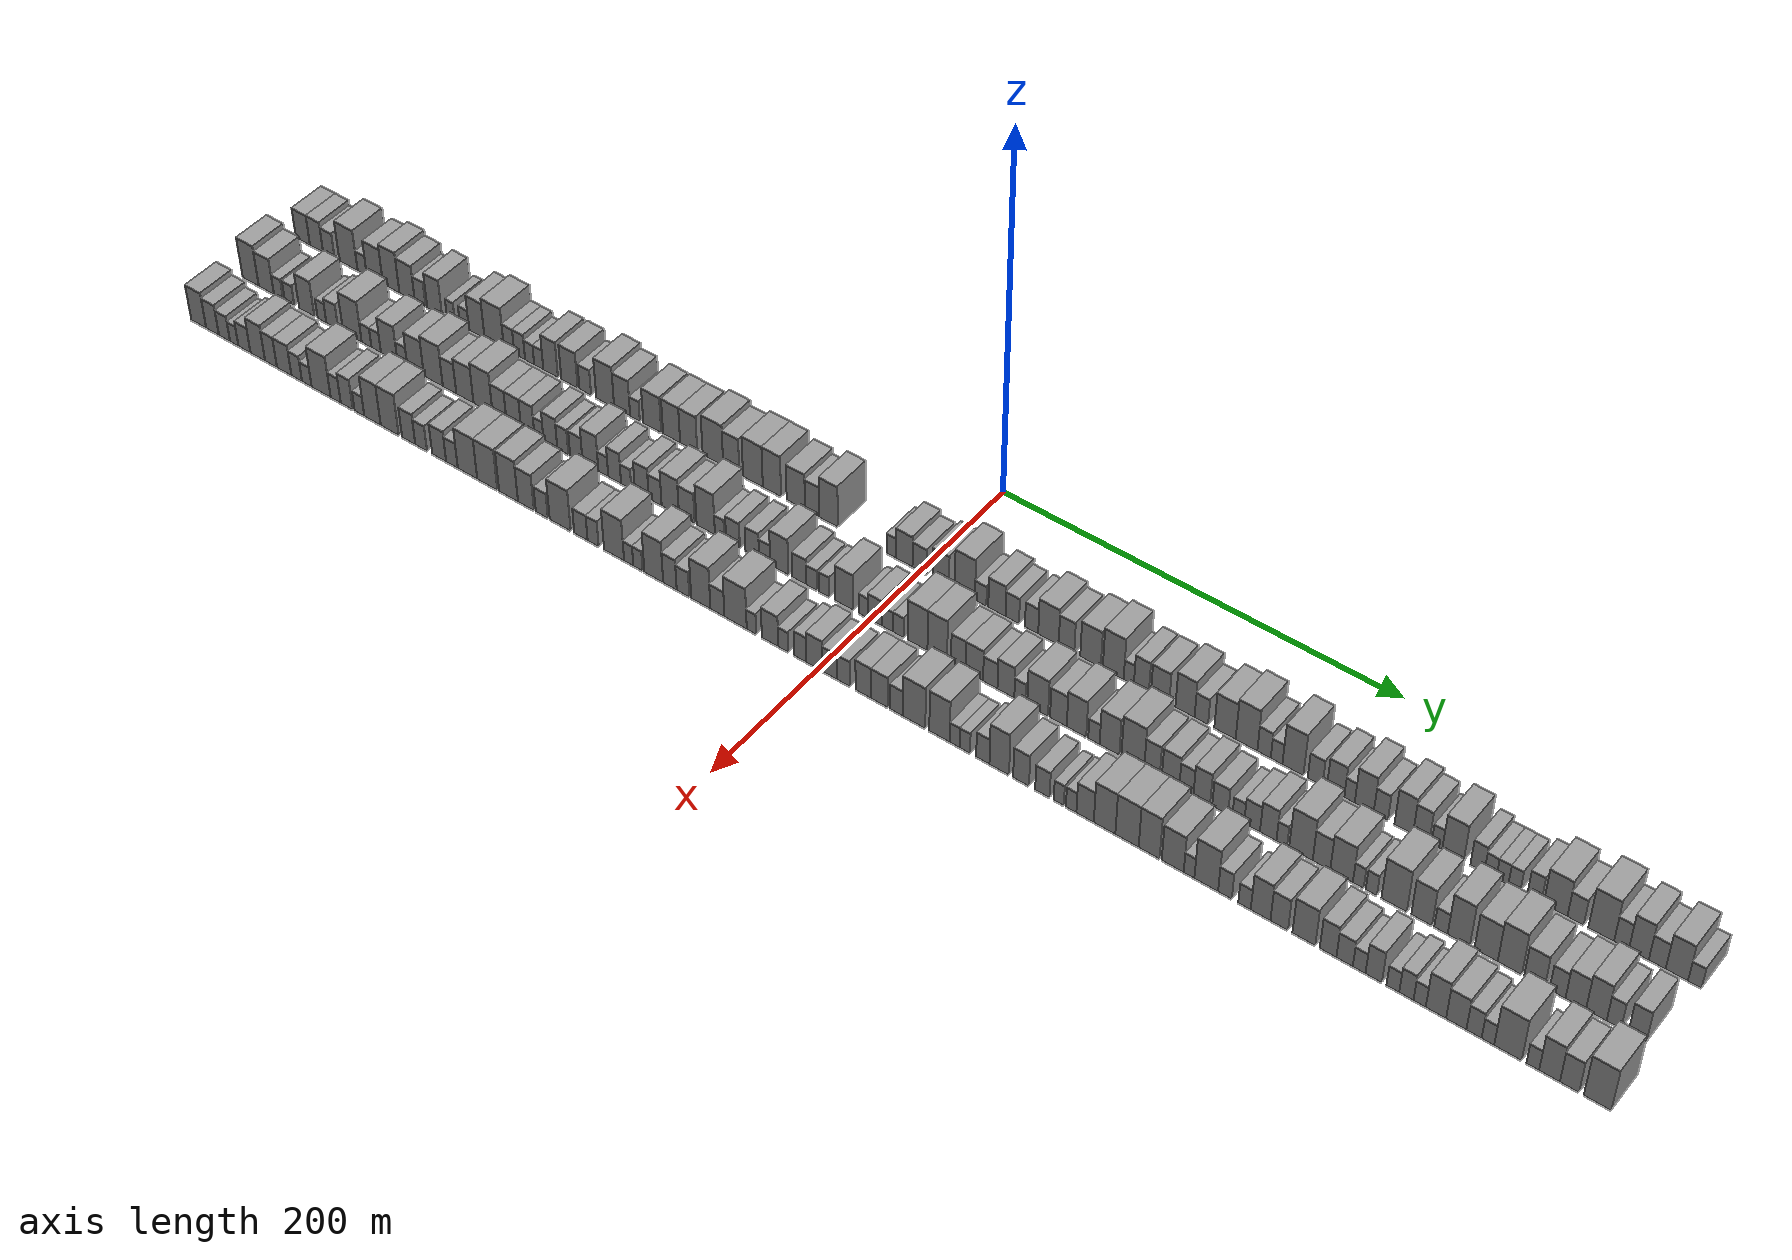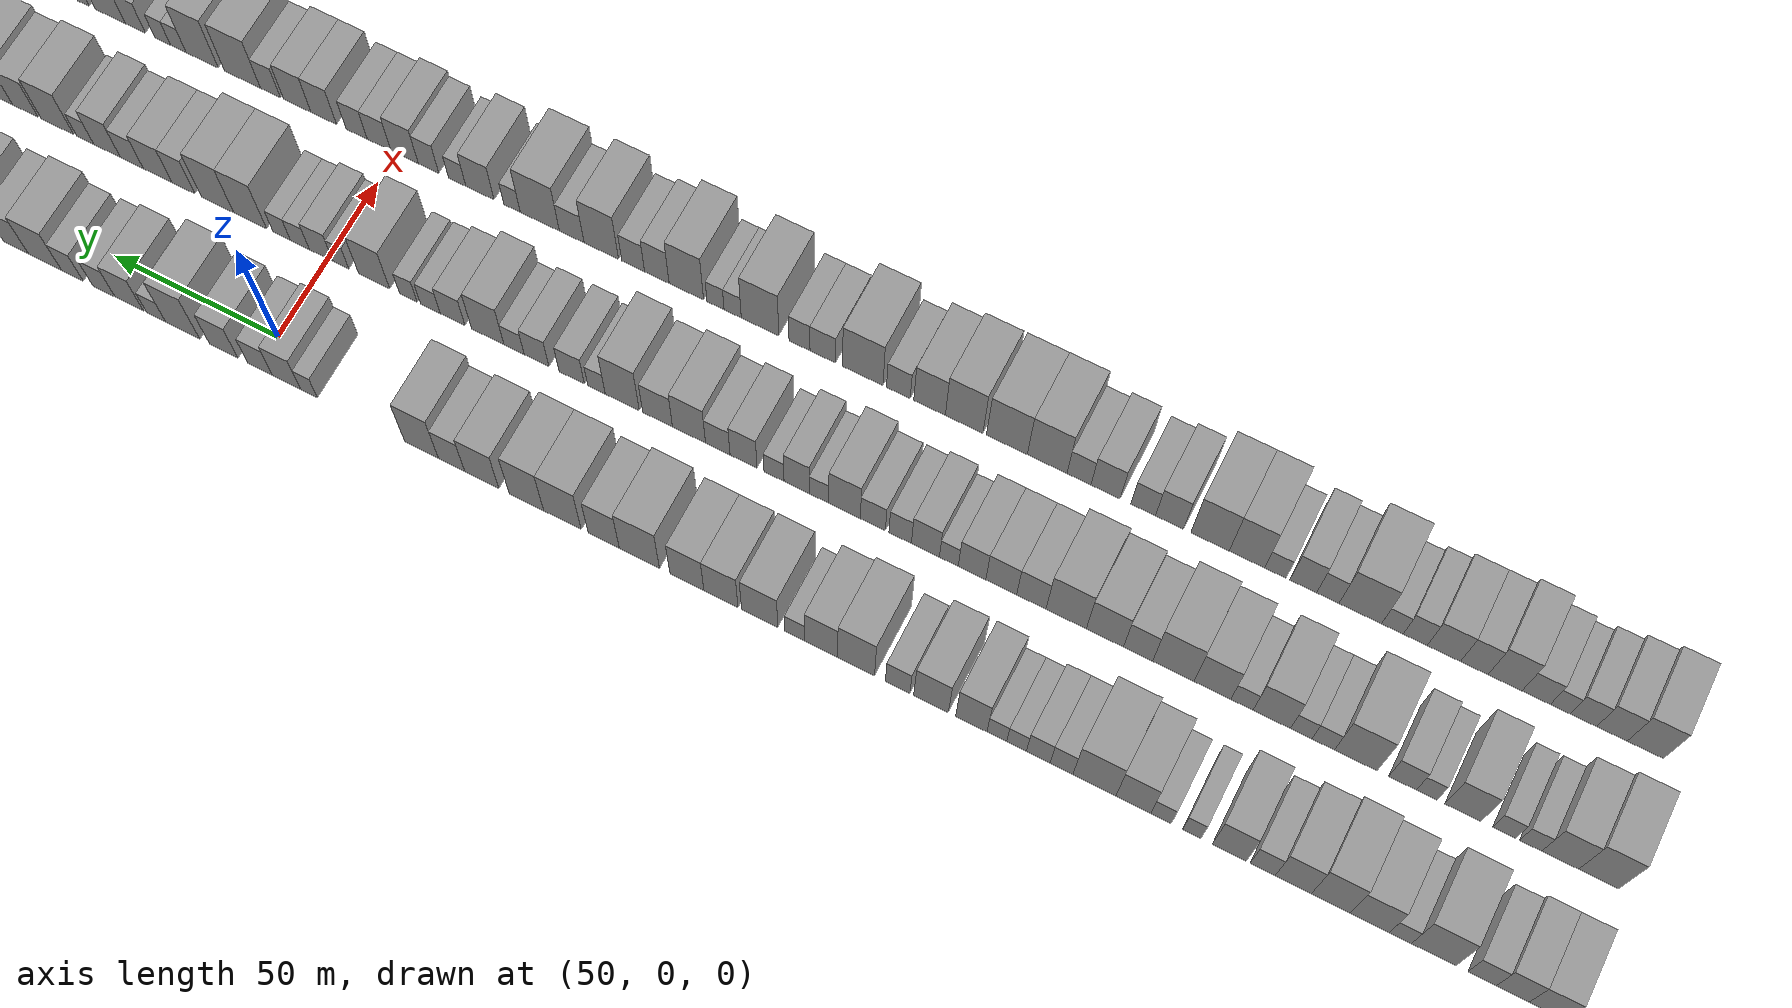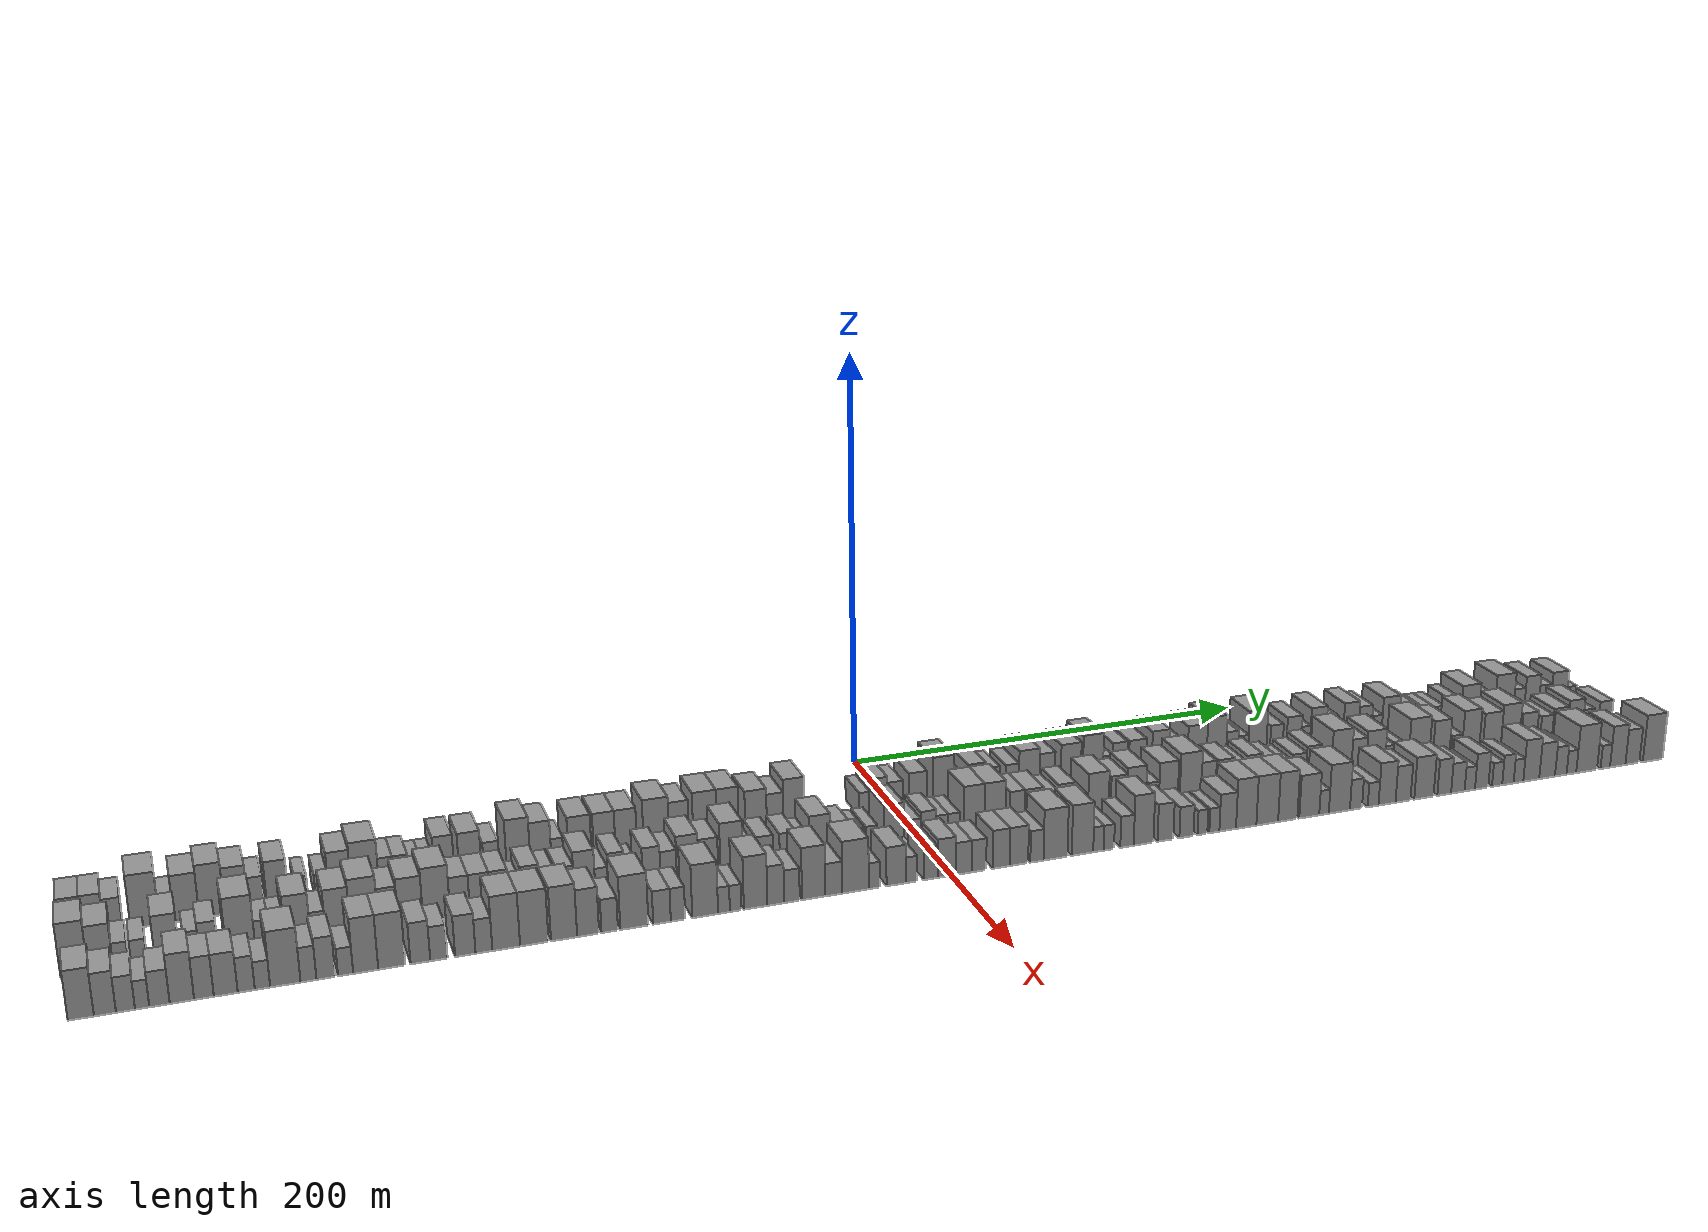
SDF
<sdf version="1.6">
 <world name="default">
  <scene>
   <sky><clouds><speed>12</speed></clouds></sky>
   <ambient>0.4 0.4 0.4 1</ambient>
   <background>0.7 0.7 0.7 1</background>
   <shadows>1</shadows>
  </scene>
  <gravity>0 0 -9.8066</gravity>
  <magnetic_field>6e-06 2.3e-05 -4.2e-05</magnetic_field>
  <physics default="0" name="default_physics" type="ode">
   <ode>
    <solver>
     <type>quick</type>
     <iters>10</iters>
     <sor>1.0</sor>
     <use_dynamic_moi_rescaling>0</use_dynamic_moi_rescaling>
    </solver>
    <constraints>
     <cfm>0</cfm>
     <erp>0.2</erp>
     <contact_max_correcting_vel>100</contact_max_correcting_vel>
     <contact_surface_layer>0.001</contact_surface_layer>
    </constraints>
   </ode>
   <max_step_size>0.004</max_step_size>
   <real_time_factor>1</real_time_factor>
   <real_time_update_rate>250</real_time_update_rate>
  </physics>
  <light name="sun" type="directional">
   <pose>0 0 10 0 0 0</pose>
   <diffuse>0.8 0.8 0.8 1</diffuse>
   <specular>0.2 0.2 0.2 1</specular>
   <attenuation>
    <range>1000</range>
    <constant>0.9</constant>
    <linear>0.01</linear>
    <quadratic>0.001</quadratic>
   </attenuation>
   <direction>-0.5 0.1 -0.9</direction>
  </light>
  <model name="building_1">
   <static>1</static>
   <pose>50.0000 -355.5543 0 0.000000 0.000000 0.000000</pose>
   <link name="link">
    <pose>0 0 9.00 0 0 0</pose>
    <collision name="collision"><geometry><box><size>20.0000 8.8914 18.0000</size></box></geometry></collision>
    <visual name="visual">
     <cast_shadows>0</cast_shadows>
     <geometry><box><size>20.0000 8.8914 18.0000</size></box></geometry>
     <material>
      <script>
       <uri>model://grey_wall/materials/scripts</uri>
       <uri>model://grey_wall/materials/textures</uri>
       <name>vrc/grey_wall</name>
      </script>
     </material>
    </visual>
   </link>
  </model>
  <model name="building_2">
   <static>1</static>
   <pose>50.0000 -346.9691 0 0.000000 0.000000 0.000000</pose>
   <link name="link">
    <pose>0 0 9.00 0 0 0</pose>
    <collision name="collision"><geometry><box><size>20.0000 8.2791 18.0000</size></box></geometry></collision>
    <visual name="visual">
     <cast_shadows>0</cast_shadows>
     <geometry><box><size>20.0000 8.2791 18.0000</size></box></geometry>
     <material>
      <script>
       <uri>model://grey_wall/materials/scripts</uri>
       <uri>model://grey_wall/materials/textures</uri>
       <name>vrc/grey_wall</name>
      </script>
     </material>
    </visual>
   </link>
  </model>
  <model name="building_3">
   <static>1</static>
   <pose>50.0000 -339.2189 0 0.000000 0.000000 0.000000</pose>
   <link name="link">
    <pose>0 0 7.50 0 0 0</pose>
    <collision name="collision"><geometry><box><size>20.0000 7.2212 15.0000</size></box></geometry></collision>
    <visual name="visual">
     <cast_shadows>0</cast_shadows>
     <geometry><box><size>20.0000 7.2212 15.0000</size></box></geometry>
     <material>
      <script>
       <uri>model://grey_wall/materials/scripts</uri>
       <uri>model://grey_wall/materials/textures</uri>
       <name>vrc/grey_wall</name>
      </script>
     </material>
    </visual>
   </link>
  </model>
  <model name="building_4">
   <static>1</static>
   <pose>50.0000 -326.9329 0 0.000000 0.000000 0.000000</pose>
   <link name="link">
    <pose>0 0 12.00 0 0 0</pose>
    <collision name="collision"><geometry><box><size>20.0000 11.3509 24.0000</size></box></geometry></collision>
    <visual name="visual">
     <cast_shadows>0</cast_shadows>
     <geometry><box><size>20.0000 11.3509 24.0000</size></box></geometry>
     <material>
      <script>
       <uri>model://grey_wall/materials/scripts</uri>
       <uri>model://grey_wall/materials/textures</uri>
       <name>vrc/grey_wall</name>
      </script>
     </material>
    </visual>
   </link>
  </model>
  <model name="building_5">
   <static>1</static>
   <pose>50.0000 -318.4150 0 0.000000 0.000000 0.000000</pose>
   <link name="link">
    <pose>0 0 6.00 0 0 0</pose>
    <collision name="collision"><geometry><box><size>20.0000 5.6850 12.0000</size></box></geometry></collision>
    <visual name="visual">
     <cast_shadows>0</cast_shadows>
     <geometry><box><size>20.0000 5.6850 12.0000</size></box></geometry>
     <material>
      <script>
       <uri>model://grey_wall/materials/scripts</uri>
       <uri>model://grey_wall/materials/textures</uri>
       <name>vrc/grey_wall</name>
      </script>
     </material>
    </visual>
   </link>
  </model>
  <model name="building_6">
   <static>1</static>
   <pose>50.0000 -310.5477 0 0.000000 0.000000 0.000000</pose>
   <link name="link">
    <pose>0 0 10.50 0 0 0</pose>
    <collision name="collision"><geometry><box><size>20.0000 10.0495 21.0000</size></box></geometry></collision>
    <visual name="visual">
     <cast_shadows>0</cast_shadows>
     <geometry><box><size>20.0000 10.0495 21.0000</size></box></geometry>
     <material>
      <script>
       <uri>model://grey_wall/materials/scripts</uri>
       <uri>model://grey_wall/materials/textures</uri>
       <name>vrc/grey_wall</name>
      </script>
     </material>
    </visual>
   </link>
  </model>
  <model name="building_7">
   <static>1</static>
   <pose>50.0000 -300.4793 0 0.000000 0.000000 0.000000</pose>
   <link name="link">
    <pose>0 0 12.00 0 0 0</pose>
    <collision name="collision"><geometry><box><size>20.0000 10.0874 24.0000</size></box></geometry></collision>
    <visual name="visual">
     <cast_shadows>0</cast_shadows>
     <geometry><box><size>20.0000 10.0874 24.0000</size></box></geometry>
     <material>
      <script>
       <uri>model://grey_wall/materials/scripts</uri>
       <uri>model://grey_wall/materials/textures</uri>
       <name>vrc/grey_wall</name>
      </script>
     </material>
    </visual>
   </link>
  </model>
  <model name="building_8">
   <static>1</static>
   <pose>50.0000 -290.7188 0 0.000000 0.000000 0.000000</pose>
   <link name="link">
    <pose>0 0 10.50 0 0 0</pose>
    <collision name="collision"><geometry><box><size>20.0000 9.4337 21.0000</size></box></geometry></collision>
    <visual name="visual">
     <cast_shadows>0</cast_shadows>
     <geometry><box><size>20.0000 9.4337 21.0000</size></box></geometry>
     <material>
      <script>
       <uri>model://grey_wall/materials/scripts</uri>
       <uri>model://grey_wall/materials/textures</uri>
       <name>vrc/grey_wall</name>
      </script>
     </material>
    </visual>
   </link>
  </model>
  <model name="building_9">
   <static>1</static>
   <pose>50.0000 -282.7231 0 0.000000 0.000000 0.000000</pose>
   <link name="link">
    <pose>0 0 7.50 0 0 0</pose>
    <collision name="collision"><geometry><box><size>20.0000 6.5577 15.0000</size></box></geometry></collision>
    <visual name="visual">
     <cast_shadows>0</cast_shadows>
     <geometry><box><size>20.0000 6.5577 15.0000</size></box></geometry>
     <material>
      <script>
       <uri>model://grey_wall/materials/scripts</uri>
       <uri>model://grey_wall/materials/textures</uri>
       <name>vrc/grey_wall</name>
      </script>
     </material>
    </visual>
   </link>
  </model>
  <model name="building_10">
   <static>1</static>
   <pose>50.0000 -273.9683 0 0.000000 0.000000 0.000000</pose>
   <link name="link">
    <pose>0 0 10.50 0 0 0</pose>
    <collision name="collision"><geometry><box><size>20.0000 8.9520 21.0000</size></box></geometry></collision>
    <visual name="visual">
     <cast_shadows>0</cast_shadows>
     <geometry><box><size>20.0000 8.9520 21.0000</size></box></geometry>
     <material>
      <script>
       <uri>model://grey_wall/materials/scripts</uri>
       <uri>model://grey_wall/materials/textures</uri>
       <name>vrc/grey_wall</name>
      </script>
     </material>
    </visual>
   </link>
  </model>
  <model name="building_11">
   <static>1</static>
   <pose>50.0000 -264.0726 0 0.000000 0.000000 0.000000</pose>
   <link name="link">
    <pose>0 0 6.00 0 0 0</pose>
    <collision name="collision"><geometry><box><size>20.0000 4.8393 12.0000</size></box></geometry></collision>
    <visual name="visual">
     <cast_shadows>0</cast_shadows>
     <geometry><box><size>20.0000 4.8393 12.0000</size></box></geometry>
     <material>
      <script>
       <uri>model://grey_wall/materials/scripts</uri>
       <uri>model://grey_wall/materials/textures</uri>
       <name>vrc/grey_wall</name>
      </script>
     </material>
    </visual>
   </link>
  </model>
  <model name="building_12">
   <static>1</static>
   <pose>50.0000 -255.9314 0 0.000000 0.000000 0.000000</pose>
   <link name="link">
    <pose>0 0 6.00 0 0 0</pose>
    <collision name="collision"><geometry><box><size>20.0000 5.4432 12.0000</size></box></geometry></collision>
    <visual name="visual">
     <cast_shadows>0</cast_shadows>
     <geometry><box><size>20.0000 5.4432 12.0000</size></box></geometry>
     <material>
      <script>
       <uri>model://grey_wall/materials/scripts</uri>
       <uri>model://grey_wall/materials/textures</uri>
       <name>vrc/grey_wall</name>
      </script>
     </material>
    </visual>
   </link>
  </model>
  <model name="building_13">
   <static>1</static>
   <pose>50.0000 -248.5627 0 0.000000 0.000000 0.000000</pose>
   <link name="link">
    <pose>0 0 10.50 0 0 0</pose>
    <collision name="collision"><geometry><box><size>20.0000 9.2942 21.0000</size></box></geometry></collision>
    <visual name="visual">
     <cast_shadows>0</cast_shadows>
     <geometry><box><size>20.0000 9.2942 21.0000</size></box></geometry>
     <material>
      <script>
       <uri>model://grey_wall/materials/scripts</uri>
       <uri>model://grey_wall/materials/textures</uri>
       <name>vrc/grey_wall</name>
      </script>
     </material>
    </visual>
   </link>
  </model>
  <model name="building_14">
   <static>1</static>
   <pose>50.0000 -238.1467 0 0.000000 0.000000 0.000000</pose>
   <link name="link">
    <pose>0 0 12.00 0 0 0</pose>
    <collision name="collision"><geometry><box><size>20.0000 11.5378 24.0000</size></box></geometry></collision>
    <visual name="visual">
     <cast_shadows>0</cast_shadows>
     <geometry><box><size>20.0000 11.5378 24.0000</size></box></geometry>
     <material>
      <script>
       <uri>model://grey_wall/materials/scripts</uri>
       <uri>model://grey_wall/materials/textures</uri>
       <name>vrc/grey_wall</name>
      </script>
     </material>
    </visual>
   </link>
  </model>
  <model name="building_15">
   <static>1</static>
   <pose>50.0000 -229.2953 0 0.000000 0.000000 0.000000</pose>
   <link name="link">
    <pose>0 0 7.50 0 0 0</pose>
    <collision name="collision"><geometry><box><size>20.0000 6.1651 15.0000</size></box></geometry></collision>
    <visual name="visual">
     <cast_shadows>0</cast_shadows>
     <geometry><box><size>20.0000 6.1651 15.0000</size></box></geometry>
     <material>
      <script>
       <uri>model://grey_wall/materials/scripts</uri>
       <uri>model://grey_wall/materials/textures</uri>
       <name>vrc/grey_wall</name>
      </script>
     </material>
    </visual>
   </link>
  </model>
  <model name="building_16">
   <static>1</static>
   <pose>50.0000 -223.0267 0 0.000000 0.000000 0.000000</pose>
   <link name="link">
    <pose>0 0 7.50 0 0 0</pose>
    <collision name="collision"><geometry><box><size>20.0000 6.3720 15.0000</size></box></geometry></collision>
    <visual name="visual">
     <cast_shadows>0</cast_shadows>
     <geometry><box><size>20.0000 6.3720 15.0000</size></box></geometry>
     <material>
      <script>
       <uri>model://grey_wall/materials/scripts</uri>
       <uri>model://grey_wall/materials/textures</uri>
       <name>vrc/grey_wall</name>
      </script>
     </material>
    </visual>
   </link>
  </model>
  <model name="building_17">
   <static>1</static>
   <pose>50.0000 -217.1712 0 0.000000 0.000000 0.000000</pose>
   <link name="link">
    <pose>0 0 6.00 0 0 0</pose>
    <collision name="collision"><geometry><box><size>20.0000 5.3390 12.0000</size></box></geometry></collision>
    <visual name="visual">
     <cast_shadows>0</cast_shadows>
     <geometry><box><size>20.0000 5.3390 12.0000</size></box></geometry>
     <material>
      <script>
       <uri>model://grey_wall/materials/scripts</uri>
       <uri>model://grey_wall/materials/textures</uri>
       <name>vrc/grey_wall</name>
      </script>
     </material>
    </visual>
   </link>
  </model>
  <model name="building_18">
   <static>1</static>
   <pose>50.0000 -211.8315 0 0.000000 0.000000 0.000000</pose>
   <link name="link">
    <pose>0 0 6.00 0 0 0</pose>
    <collision name="collision"><geometry><box><size>20.0000 5.3403 12.0000</size></box></geometry></collision>
    <visual name="visual">
     <cast_shadows>0</cast_shadows>
     <geometry><box><size>20.0000 5.3403 12.0000</size></box></geometry>
     <material>
      <script>
       <uri>model://grey_wall/materials/scripts</uri>
       <uri>model://grey_wall/materials/textures</uri>
       <name>vrc/grey_wall</name>
      </script>
     </material>
    </visual>
   </link>
  </model>
  <model name="building_19">
   <static>1</static>
   <pose>50.0000 -204.9044 0 0.000000 0.000000 0.000000</pose>
   <link name="link">
    <pose>0 0 10.50 0 0 0</pose>
    <collision name="collision"><geometry><box><size>20.0000 8.5139 21.0000</size></box></geometry></collision>
    <visual name="visual">
     <cast_shadows>0</cast_shadows>
     <geometry><box><size>20.0000 8.5139 21.0000</size></box></geometry>
     <material>
      <script>
       <uri>model://grey_wall/materials/scripts</uri>
       <uri>model://grey_wall/materials/textures</uri>
       <name>vrc/grey_wall</name>
      </script>
     </material>
    </visual>
   </link>
  </model>
  <model name="building_20">
   <static>1</static>
   <pose>50.0000 -193.8881 0 0.000000 0.000000 0.000000</pose>
   <link name="link">
    <pose>0 0 10.50 0 0 0</pose>
    <collision name="collision"><geometry><box><size>20.0000 9.5186 21.0000</size></box></geometry></collision>
    <visual name="visual">
     <cast_shadows>0</cast_shadows>
     <geometry><box><size>20.0000 9.5186 21.0000</size></box></geometry>
     <material>
      <script>
       <uri>model://grey_wall/materials/scripts</uri>
       <uri>model://grey_wall/materials/textures</uri>
       <name>vrc/grey_wall</name>
      </script>
     </material>
    </visual>
   </link>
  </model>
  <model name="building_21">
   <static>1</static>
   <pose>50.0000 -184.7525 0 0.000000 0.000000 0.000000</pose>
   <link name="link">
    <pose>0 0 7.50 0 0 0</pose>
    <collision name="collision"><geometry><box><size>20.0000 6.7527 15.0000</size></box></geometry></collision>
    <visual name="visual">
     <cast_shadows>0</cast_shadows>
     <geometry><box><size>20.0000 6.7527 15.0000</size></box></geometry>
     <material>
      <script>
       <uri>model://grey_wall/materials/scripts</uri>
       <uri>model://grey_wall/materials/textures</uri>
       <name>vrc/grey_wall</name>
      </script>
     </material>
    </visual>
   </link>
  </model>
  <model name="building_22">
   <static>1</static>
   <pose>50.0000 -173.2291 0 0.000000 0.000000 0.000000</pose>
   <link name="link">
    <pose>0 0 12.00 0 0 0</pose>
    <collision name="collision"><geometry><box><size>20.0000 10.2941 24.0000</size></box></geometry></collision>
    <visual name="visual">
     <cast_shadows>0</cast_shadows>
     <geometry><box><size>20.0000 10.2941 24.0000</size></box></geometry>
     <material>
      <script>
       <uri>model://grey_wall/materials/scripts</uri>
       <uri>model://grey_wall/materials/textures</uri>
       <name>vrc/grey_wall</name>
      </script>
     </material>
    </visual>
   </link>
  </model>
  <model name="building_23">
   <static>1</static>
   <pose>50.0000 -163.5071 0 0.000000 0.000000 0.000000</pose>
   <link name="link">
    <pose>0 0 10.50 0 0 0</pose>
    <collision name="collision"><geometry><box><size>20.0000 9.1499 21.0000</size></box></geometry></collision>
    <visual name="visual">
     <cast_shadows>0</cast_shadows>
     <geometry><box><size>20.0000 9.1499 21.0000</size></box></geometry>
     <material>
      <script>
       <uri>model://grey_wall/materials/scripts</uri>
       <uri>model://grey_wall/materials/textures</uri>
       <name>vrc/grey_wall</name>
      </script>
     </material>
    </visual>
   </link>
  </model>
  <model name="building_24">
   <static>1</static>
   <pose>50.0000 -156.1976 0 0.000000 0.000000 0.000000</pose>
   <link name="link">
    <pose>0 0 6.00 0 0 0</pose>
    <collision name="collision"><geometry><box><size>20.0000 5.4691 12.0000</size></box></geometry></collision>
    <visual name="visual">
     <cast_shadows>0</cast_shadows>
     <geometry><box><size>20.0000 5.4691 12.0000</size></box></geometry>
     <material>
      <script>
       <uri>model://grey_wall/materials/scripts</uri>
       <uri>model://grey_wall/materials/textures</uri>
       <name>vrc/grey_wall</name>
      </script>
     </material>
    </visual>
   </link>
  </model>
  <model name="building_25">
   <static>1</static>
   <pose>50.0000 -146.3815 0 0.000000 0.000000 0.000000</pose>
   <link name="link">
    <pose>0 0 10.50 0 0 0</pose>
    <collision name="collision"><geometry><box><size>20.0000 10.1630 21.0000</size></box></geometry></collision>
    <visual name="visual">
     <cast_shadows>0</cast_shadows>
     <geometry><box><size>20.0000 10.1630 21.0000</size></box></geometry>
     <material>
      <script>
       <uri>model://grey_wall/materials/scripts</uri>
       <uri>model://grey_wall/materials/textures</uri>
       <name>vrc/grey_wall</name>
      </script>
     </material>
    </visual>
   </link>
  </model>
  <model name="building_26">
   <static>1</static>
   <pose>50.0000 -135.4872 0 0.000000 0.000000 0.000000</pose>
   <link name="link">
    <pose>0 0 10.50 0 0 0</pose>
    <collision name="collision"><geometry><box><size>20.0000 9.6257 21.0000</size></box></geometry></collision>
    <visual name="visual">
     <cast_shadows>0</cast_shadows>
     <geometry><box><size>20.0000 9.6257 21.0000</size></box></geometry>
     <material>
      <script>
       <uri>model://grey_wall/materials/scripts</uri>
       <uri>model://grey_wall/materials/textures</uri>
       <name>vrc/grey_wall</name>
      </script>
     </material>
    </visual>
   </link>
  </model>
  <model name="building_27">
   <static>1</static>
   <pose>50.0000 -125.8723 0 0.000000 0.000000 0.000000</pose>
   <link name="link">
    <pose>0 0 10.50 0 0 0</pose>
    <collision name="collision"><geometry><box><size>20.0000 9.6040 21.0000</size></box></geometry></collision>
    <visual name="visual">
     <cast_shadows>0</cast_shadows>
     <geometry><box><size>20.0000 9.6040 21.0000</size></box></geometry>
     <material>
      <script>
       <uri>model://grey_wall/materials/scripts</uri>
       <uri>model://grey_wall/materials/textures</uri>
       <name>vrc/grey_wall</name>
      </script>
     </material>
    </visual>
   </link>
  </model>
  <model name="building_28">
   <static>1</static>
   <pose>50.0000 -112.3370 0 0.000000 0.000000 0.000000</pose>
   <link name="link">
    <pose>0 0 12.00 0 0 0</pose>
    <collision name="collision"><geometry><box><size>20.0000 11.4666 24.0000</size></box></geometry></collision>
    <visual name="visual">
     <cast_shadows>0</cast_shadows>
     <geometry><box><size>20.0000 11.4666 24.0000</size></box></geometry>
     <material>
      <script>
       <uri>model://grey_wall/materials/scripts</uri>
       <uri>model://grey_wall/materials/textures</uri>
       <name>vrc/grey_wall</name>
      </script>
     </material>
    </visual>
   </link>
  </model>
  <model name="building_29">
   <static>1</static>
   <pose>50.0000 -102.1314 0 0.000000 0.000000 0.000000</pose>
   <link name="link">
    <pose>0 0 10.50 0 0 0</pose>
    <collision name="collision"><geometry><box><size>20.0000 8.9447 21.0000</size></box></geometry></collision>
    <visual name="visual">
     <cast_shadows>0</cast_shadows>
     <geometry><box><size>20.0000 8.9447 21.0000</size></box></geometry>
     <material>
      <script>
       <uri>model://grey_wall/materials/scripts</uri>
       <uri>model://grey_wall/materials/textures</uri>
       <name>vrc/grey_wall</name>
      </script>
     </material>
    </visual>
   </link>
  </model>
  <model name="building_30">
   <static>1</static>
   <pose>50.0000 -90.2336 0 0.000000 0.000000 0.000000</pose>
   <link name="link">
    <pose>0 0 12.00 0 0 0</pose>
    <collision name="collision"><geometry><box><size>20.0000 10.8509 24.0000</size></box></geometry></collision>
    <visual name="visual">
     <cast_shadows>0</cast_shadows>
     <geometry><box><size>20.0000 10.8509 24.0000</size></box></geometry>
     <material>
      <script>
       <uri>model://grey_wall/materials/scripts</uri>
       <uri>model://grey_wall/materials/textures</uri>
       <name>vrc/grey_wall</name>
      </script>
     </material>
    </visual>
   </link>
  </model>
  <model name="building_31">
   <static>1</static>
   <pose>50.0000 -79.8051 0 0.000000 0.000000 0.000000</pose>
   <link name="link">
    <pose>0 0 12.00 0 0 0</pose>
    <collision name="collision"><geometry><box><size>20.0000 10.0059 24.0000</size></box></geometry></collision>
    <visual name="visual">
     <cast_shadows>0</cast_shadows>
     <geometry><box><size>20.0000 10.0059 24.0000</size></box></geometry>
     <material>
      <script>
       <uri>model://grey_wall/materials/scripts</uri>
       <uri>model://grey_wall/materials/textures</uri>
       <name>vrc/grey_wall</name>
      </script>
     </material>
    </visual>
   </link>
  </model>
  <model name="building_32">
   <static>1</static>
   <pose>50.0000 -66.7975 0 0.000000 0.000000 0.000000</pose>
   <link name="link">
    <pose>0 0 10.50 0 0 0</pose>
    <collision name="collision"><geometry><box><size>20.0000 10.0093 21.0000</size></box></geometry></collision>
    <visual name="visual">
     <cast_shadows>0</cast_shadows>
     <geometry><box><size>20.0000 10.0093 21.0000</size></box></geometry>
     <material>
      <script>
       <uri>model://grey_wall/materials/scripts</uri>
       <uri>model://grey_wall/materials/textures</uri>
       <name>vrc/grey_wall</name>
      </script>
     </material>
    </visual>
   </link>
  </model>
  <model name="building_33">
   <static>1</static>
   <pose>50.0000 -57.9215 0 0.000000 0.000000 0.000000</pose>
   <link name="link">
    <pose>0 0 9.00 0 0 0</pose>
    <collision name="collision"><geometry><box><size>20.0000 7.7427 18.0000</size></box></geometry></collision>
    <visual name="visual">
     <cast_shadows>0</cast_shadows>
     <geometry><box><size>20.0000 7.7427 18.0000</size></box></geometry>
     <material>
      <script>
       <uri>model://grey_wall/materials/scripts</uri>
       <uri>model://grey_wall/materials/textures</uri>
       <name>vrc/grey_wall</name>
      </script>
     </material>
    </visual>
   </link>
  </model>
  <model name="building_34">
   <static>1</static>
   <pose>50.0000 -49.0845 0 0.000000 0.000000 0.000000</pose>
   <link name="link">
    <pose>0 0 12.00 0 0 0</pose>
    <collision name="collision"><geometry><box><size>20.0000 9.9313 24.0000</size></box></geometry></collision>
    <visual name="visual">
     <cast_shadows>0</cast_shadows>
     <geometry><box><size>20.0000 9.9313 24.0000</size></box></geometry>
     <material>
      <script>
       <uri>model://grey_wall/materials/scripts</uri>
       <uri>model://grey_wall/materials/textures</uri>
       <name>vrc/grey_wall</name>
      </script>
     </material>
    </visual>
   </link>
  </model>
  <model name="building_35">
   <static>1</static>
   <pose>50.0000 -15.6413 0 0.000000 0.000000 0.000000</pose>
   <link name="link">
    <pose>0 0 6.00 0 0 0</pose>
    <collision name="collision"><geometry><box><size>20.0000 4.9850 12.0000</size></box></geometry></collision>
    <visual name="visual">
     <cast_shadows>0</cast_shadows>
     <geometry><box><size>20.0000 4.9850 12.0000</size></box></geometry>
     <material>
      <script>
       <uri>model://grey_wall/materials/scripts</uri>
       <uri>model://grey_wall/materials/textures</uri>
       <name>vrc/grey_wall</name>
      </script>
     </material>
    </visual>
   </link>
  </model>
  <model name="building_36">
   <static>1</static>
   <pose>50.0000 -8.9011 0 0.000000 0.000000 0.000000</pose>
   <link name="link">
    <pose>0 0 9.00 0 0 0</pose>
    <collision name="collision"><geometry><box><size>20.0000 8.4952 18.0000</size></box></geometry></collision>
    <visual name="visual">
     <cast_shadows>0</cast_shadows>
     <geometry><box><size>20.0000 8.4952 18.0000</size></box></geometry>
     <material>
      <script>
       <uri>model://grey_wall/materials/scripts</uri>
       <uri>model://grey_wall/materials/textures</uri>
       <name>vrc/grey_wall</name>
      </script>
     </material>
    </visual>
   </link>
  </model>
  <model name="building_37">
   <static>1</static>
   <pose>50.0000 -0.9262 0 0.000000 0.000000 0.000000</pose>
   <link name="link">
    <pose>0 0 7.50 0 0 0</pose>
    <collision name="collision"><geometry><box><size>20.0000 7.4545 15.0000</size></box></geometry></collision>
    <visual name="visual">
     <cast_shadows>0</cast_shadows>
     <geometry><box><size>20.0000 7.4545 15.0000</size></box></geometry>
     <material>
      <script>
       <uri>model://grey_wall/materials/scripts</uri>
       <uri>model://grey_wall/materials/textures</uri>
       <name>vrc/grey_wall</name>
      </script>
     </material>
    </visual>
   </link>
  </model>
  <model name="building_38">
   <static>1</static>
   <pose>50.0000 10.1009 0 0.000000 0.000000 0.000000</pose>
   <link name="link">
    <pose>0 0 9.00 0 0 0</pose>
    <collision name="collision"><geometry><box><size>20.0000 8.5998 18.0000</size></box></geometry></collision>
    <visual name="visual">
     <cast_shadows>0</cast_shadows>
     <geometry><box><size>20.0000 8.5998 18.0000</size></box></geometry>
     <material>
      <script>
       <uri>model://grey_wall/materials/scripts</uri>
       <uri>model://grey_wall/materials/textures</uri>
       <name>vrc/grey_wall</name>
      </script>
     </material>
    </visual>
   </link>
  </model>
  <model name="building_39">
   <static>1</static>
   <pose>50.0000 22.5908 0 0.000000 0.000000 0.000000</pose>
   <link name="link">
    <pose>0 0 12.00 0 0 0</pose>
    <collision name="collision"><geometry><box><size>20.0000 10.3801 24.0000</size></box></geometry></collision>
    <visual name="visual">
     <cast_shadows>0</cast_shadows>
     <geometry><box><size>20.0000 10.3801 24.0000</size></box></geometry>
     <material>
      <script>
       <uri>model://grey_wall/materials/scripts</uri>
       <uri>model://grey_wall/materials/textures</uri>
       <name>vrc/grey_wall</name>
      </script>
     </material>
    </visual>
   </link>
  </model>
  <model name="building_40">
   <static>1</static>
   <pose>50.0000 30.6912 0 0.000000 0.000000 0.000000</pose>
   <link name="link">
    <pose>0 0 6.00 0 0 0</pose>
    <collision name="collision"><geometry><box><size>20.0000 5.8206 12.0000</size></box></geometry></collision>
    <visual name="visual">
     <cast_shadows>0</cast_shadows>
     <geometry><box><size>20.0000 5.8206 12.0000</size></box></geometry>
     <material>
      <script>
       <uri>model://grey_wall/materials/scripts</uri>
       <uri>model://grey_wall/materials/textures</uri>
       <name>vrc/grey_wall</name>
      </script>
     </material>
    </visual>
   </link>
  </model>
  <model name="building_41">
   <static>1</static>
   <pose>50.0000 39.0023 0 0.000000 0.000000 0.000000</pose>
   <link name="link">
    <pose>0 0 9.00 0 0 0</pose>
    <collision name="collision"><geometry><box><size>20.0000 8.8015 18.0000</size></box></geometry></collision>
    <visual name="visual">
     <cast_shadows>0</cast_shadows>
     <geometry><box><size>20.0000 8.8015 18.0000</size></box></geometry>
     <material>
      <script>
       <uri>model://grey_wall/materials/scripts</uri>
       <uri>model://grey_wall/materials/textures</uri>
       <name>vrc/grey_wall</name>
      </script>
     </material>
    </visual>
   </link>
  </model>
  <model name="building_42">
   <static>1</static>
   <pose>50.0000 46.8425 0 0.000000 0.000000 0.000000</pose>
   <link name="link">
    <pose>0 0 7.50 0 0 0</pose>
    <collision name="collision"><geometry><box><size>20.0000 6.8788 15.0000</size></box></geometry></collision>
    <visual name="visual">
     <cast_shadows>0</cast_shadows>
     <geometry><box><size>20.0000 6.8788 15.0000</size></box></geometry>
     <material>
      <script>
       <uri>model://grey_wall/materials/scripts</uri>
       <uri>model://grey_wall/materials/textures</uri>
       <name>vrc/grey_wall</name>
      </script>
     </material>
    </visual>
   </link>
  </model>
  <model name="building_43">
   <static>1</static>
   <pose>50.0000 56.6314 0 0.000000 0.000000 0.000000</pose>
   <link name="link">
    <pose>0 0 7.50 0 0 0</pose>
    <collision name="collision"><geometry><box><size>20.0000 6.6989 15.0000</size></box></geometry></collision>
    <visual name="visual">
     <cast_shadows>0</cast_shadows>
     <geometry><box><size>20.0000 6.6989 15.0000</size></box></geometry>
     <material>
      <script>
       <uri>model://grey_wall/materials/scripts</uri>
       <uri>model://grey_wall/materials/textures</uri>
       <name>vrc/grey_wall</name>
      </script>
     </material>
    </visual>
   </link>
  </model>
  <model name="building_44">
   <static>1</static>
   <pose>50.0000 65.1340 0 0.000000 0.000000 0.000000</pose>
   <link name="link">
    <pose>0 0 10.50 0 0 0</pose>
    <collision name="collision"><geometry><box><size>20.0000 10.3063 21.0000</size></box></geometry></collision>
    <visual name="visual">
     <cast_shadows>0</cast_shadows>
     <geometry><box><size>20.0000 10.3063 21.0000</size></box></geometry>
     <material>
      <script>
       <uri>model://grey_wall/materials/scripts</uri>
       <uri>model://grey_wall/materials/textures</uri>
       <name>vrc/grey_wall</name>
      </script>
     </material>
    </visual>
   </link>
  </model>
  <model name="building_45">
   <static>1</static>
   <pose>50.0000 74.1907 0 0.000000 0.000000 0.000000</pose>
   <link name="link">
    <pose>0 0 9.00 0 0 0</pose>
    <collision name="collision"><geometry><box><size>20.0000 7.8071 18.0000</size></box></geometry></collision>
    <visual name="visual">
     <cast_shadows>0</cast_shadows>
     <geometry><box><size>20.0000 7.8071 18.0000</size></box></geometry>
     <material>
      <script>
       <uri>model://grey_wall/materials/scripts</uri>
       <uri>model://grey_wall/materials/textures</uri>
       <name>vrc/grey_wall</name>
      </script>
     </material>
    </visual>
   </link>
  </model>
  <model name="building_46">
   <static>1</static>
   <pose>50.0000 86.1909 0 0.000000 0.000000 0.000000</pose>
   <link name="link">
    <pose>0 0 10.50 0 0 0</pose>
    <collision name="collision"><geometry><box><size>20.0000 10.1934 21.0000</size></box></geometry></collision>
    <visual name="visual">
     <cast_shadows>0</cast_shadows>
     <geometry><box><size>20.0000 10.1934 21.0000</size></box></geometry>
     <material>
      <script>
       <uri>model://grey_wall/materials/scripts</uri>
       <uri>model://grey_wall/materials/textures</uri>
       <name>vrc/grey_wall</name>
      </script>
     </material>
    </visual>
   </link>
  </model>
  <model name="building_47">
   <static>1</static>
   <pose>50.0000 97.4486 0 0.000000 0.000000 0.000000</pose>
   <link name="link">
    <pose>0 0 12.00 0 0 0</pose>
    <collision name="collision"><geometry><box><size>20.0000 10.3219 24.0000</size></box></geometry></collision>
    <visual name="visual">
     <cast_shadows>0</cast_shadows>
     <geometry><box><size>20.0000 10.3219 24.0000</size></box></geometry>
     <material>
      <script>
       <uri>model://grey_wall/materials/scripts</uri>
       <uri>model://grey_wall/materials/textures</uri>
       <name>vrc/grey_wall</name>
      </script>
     </material>
    </visual>
   </link>
  </model>
  <model name="building_48">
   <static>1</static>
   <pose>50.0000 105.1076 0 0.000000 0.000000 0.000000</pose>
   <link name="link">
    <pose>0 0 6.00 0 0 0</pose>
    <collision name="collision"><geometry><box><size>20.0000 4.9961 12.0000</size></box></geometry></collision>
    <visual name="visual">
     <cast_shadows>0</cast_shadows>
     <geometry><box><size>20.0000 4.9961 12.0000</size></box></geometry>
     <material>
      <script>
       <uri>model://grey_wall/materials/scripts</uri>
       <uri>model://grey_wall/materials/textures</uri>
       <name>vrc/grey_wall</name>
      </script>
     </material>
    </visual>
   </link>
  </model>
  <model name="building_49">
   <static>1</static>
   <pose>50.0000 111.2825 0 0.000000 0.000000 0.000000</pose>
   <link name="link">
    <pose>0 0 9.00 0 0 0</pose>
    <collision name="collision"><geometry><box><size>20.0000 7.3538 18.0000</size></box></geometry></collision>
    <visual name="visual">
     <cast_shadows>0</cast_shadows>
     <geometry><box><size>20.0000 7.3538 18.0000</size></box></geometry>
     <material>
      <script>
       <uri>model://grey_wall/materials/scripts</uri>
       <uri>model://grey_wall/materials/textures</uri>
       <name>vrc/grey_wall</name>
      </script>
     </material>
    </visual>
   </link>
  </model>
  <model name="building_50">
   <static>1</static>
   <pose>50.0000 120.4251 0 0.000000 0.000000 0.000000</pose>
   <link name="link">
    <pose>0 0 9.00 0 0 0</pose>
    <collision name="collision"><geometry><box><size>20.0000 8.9313 18.0000</size></box></geometry></collision>
    <visual name="visual">
     <cast_shadows>0</cast_shadows>
     <geometry><box><size>20.0000 8.9313 18.0000</size></box></geometry>
     <material>
      <script>
       <uri>model://grey_wall/materials/scripts</uri>
       <uri>model://grey_wall/materials/textures</uri>
       <name>vrc/grey_wall</name>
      </script>
     </material>
    </visual>
   </link>
  </model>
  <model name="building_51">
   <static>1</static>
   <pose>50.0000 132.5231 0 0.000000 0.000000 0.000000</pose>
   <link name="link">
    <pose>0 0 10.50 0 0 0</pose>
    <collision name="collision"><geometry><box><size>20.0000 9.2649 21.0000</size></box></geometry></collision>
    <visual name="visual">
     <cast_shadows>0</cast_shadows>
     <geometry><box><size>20.0000 9.2649 21.0000</size></box></geometry>
     <material>
      <script>
       <uri>model://grey_wall/materials/scripts</uri>
       <uri>model://grey_wall/materials/textures</uri>
       <name>vrc/grey_wall</name>
      </script>
     </material>
    </visual>
   </link>
  </model>
  <model name="building_52">
   <static>1</static>
   <pose>50.0000 140.4135 0 0.000000 0.000000 0.000000</pose>
   <link name="link">
    <pose>0 0 7.50 0 0 0</pose>
    <collision name="collision"><geometry><box><size>20.0000 6.5158 15.0000</size></box></geometry></collision>
    <visual name="visual">
     <cast_shadows>0</cast_shadows>
     <geometry><box><size>20.0000 6.5158 15.0000</size></box></geometry>
     <material>
      <script>
       <uri>model://grey_wall/materials/scripts</uri>
       <uri>model://grey_wall/materials/textures</uri>
       <name>vrc/grey_wall</name>
      </script>
     </material>
    </visual>
   </link>
  </model>
  <model name="building_53">
   <static>1</static>
   <pose>50.0000 151.7754 0 0.000000 0.000000 0.000000</pose>
   <link name="link">
    <pose>0 0 10.50 0 0 0</pose>
    <collision name="collision"><geometry><box><size>20.0000 10.2081 21.0000</size></box></geometry></collision>
    <visual name="visual">
     <cast_shadows>0</cast_shadows>
     <geometry><box><size>20.0000 10.2081 21.0000</size></box></geometry>
     <material>
      <script>
       <uri>model://grey_wall/materials/scripts</uri>
       <uri>model://grey_wall/materials/textures</uri>
       <name>vrc/grey_wall</name>
      </script>
     </material>
    </visual>
   </link>
  </model>
  <model name="building_54">
   <static>1</static>
   <pose>50.0000 162.0459 0 0.000000 0.000000 0.000000</pose>
   <link name="link">
    <pose>0 0 12.00 0 0 0</pose>
    <collision name="collision"><geometry><box><size>20.0000 10.3329 24.0000</size></box></geometry></collision>
    <visual name="visual">
     <cast_shadows>0</cast_shadows>
     <geometry><box><size>20.0000 10.3329 24.0000</size></box></geometry>
     <material>
      <script>
       <uri>model://grey_wall/materials/scripts</uri>
       <uri>model://grey_wall/materials/textures</uri>
       <name>vrc/grey_wall</name>
      </script>
     </material>
    </visual>
   </link>
  </model>
  <model name="building_55">
   <static>1</static>
   <pose>50.0000 170.3874 0 0.000000 0.000000 0.000000</pose>
   <link name="link">
    <pose>0 0 7.50 0 0 0</pose>
    <collision name="collision"><geometry><box><size>20.0000 6.3500 15.0000</size></box></geometry></collision>
    <visual name="visual">
     <cast_shadows>0</cast_shadows>
     <geometry><box><size>20.0000 6.3500 15.0000</size></box></geometry>
     <material>
      <script>
       <uri>model://grey_wall/materials/scripts</uri>
       <uri>model://grey_wall/materials/textures</uri>
       <name>vrc/grey_wall</name>
      </script>
     </material>
    </visual>
   </link>
  </model>
  <model name="building_56">
   <static>1</static>
   <pose>50.0000 176.3052 0 0.000000 0.000000 0.000000</pose>
   <link name="link">
    <pose>0 0 6.00 0 0 0</pose>
    <collision name="collision"><geometry><box><size>20.0000 5.4856 12.0000</size></box></geometry></collision>
    <visual name="visual">
     <cast_shadows>0</cast_shadows>
     <geometry><box><size>20.0000 5.4856 12.0000</size></box></geometry>
     <material>
      <script>
       <uri>model://grey_wall/materials/scripts</uri>
       <uri>model://grey_wall/materials/textures</uri>
       <name>vrc/grey_wall</name>
      </script>
     </material>
    </visual>
   </link>
  </model>
  <model name="building_57">
   <static>1</static>
   <pose>50.0000 183.9817 0 0.000000 0.000000 0.000000</pose>
   <link name="link">
    <pose>0 0 12.00 0 0 0</pose>
    <collision name="collision"><geometry><box><size>20.0000 9.8675 24.0000</size></box></geometry></collision>
    <visual name="visual">
     <cast_shadows>0</cast_shadows>
     <geometry><box><size>20.0000 9.8675 24.0000</size></box></geometry>
     <material>
      <script>
       <uri>model://grey_wall/materials/scripts</uri>
       <uri>model://grey_wall/materials/textures</uri>
       <name>vrc/grey_wall</name>
      </script>
     </material>
    </visual>
   </link>
  </model>
  <model name="building_58">
   <static>1</static>
   <pose>50.0000 194.3728 0 0.000000 0.000000 0.000000</pose>
   <link name="link">
    <pose>0 0 7.50 0 0 0</pose>
    <collision name="collision"><geometry><box><size>20.0000 6.9147 15.0000</size></box></geometry></collision>
    <visual name="visual">
     <cast_shadows>0</cast_shadows>
     <geometry><box><size>20.0000 6.9147 15.0000</size></box></geometry>
     <material>
      <script>
       <uri>model://grey_wall/materials/scripts</uri>
       <uri>model://grey_wall/materials/textures</uri>
       <name>vrc/grey_wall</name>
      </script>
     </material>
    </visual>
   </link>
  </model>
  <model name="building_59">
   <static>1</static>
   <pose>50.0000 203.8726 0 0.000000 0.000000 0.000000</pose>
   <link name="link">
    <pose>0 0 9.00 0 0 0</pose>
    <collision name="collision"><geometry><box><size>20.0000 8.0849 18.0000</size></box></geometry></collision>
    <visual name="visual">
     <cast_shadows>0</cast_shadows>
     <geometry><box><size>20.0000 8.0849 18.0000</size></box></geometry>
     <material>
      <script>
       <uri>model://grey_wall/materials/scripts</uri>
       <uri>model://grey_wall/materials/textures</uri>
       <name>vrc/grey_wall</name>
      </script>
     </material>
    </visual>
   </link>
  </model>
  <model name="building_60">
   <static>1</static>
   <pose>50.0000 210.3365 0 0.000000 0.000000 0.000000</pose>
   <link name="link">
    <pose>0 0 6.00 0 0 0</pose>
    <collision name="collision"><geometry><box><size>20.0000 4.8430 12.0000</size></box></geometry></collision>
    <visual name="visual">
     <cast_shadows>0</cast_shadows>
     <geometry><box><size>20.0000 4.8430 12.0000</size></box></geometry>
     <material>
      <script>
       <uri>model://grey_wall/materials/scripts</uri>
       <uri>model://grey_wall/materials/textures</uri>
       <name>vrc/grey_wall</name>
      </script>
     </material>
    </visual>
   </link>
  </model>
  <model name="building_61">
   <static>1</static>
   <pose>50.0000 217.1121 0 0.000000 0.000000 0.000000</pose>
   <link name="link">
    <pose>0 0 10.50 0 0 0</pose>
    <collision name="collision"><geometry><box><size>20.0000 8.7081 21.0000</size></box></geometry></collision>
    <visual name="visual">
     <cast_shadows>0</cast_shadows>
     <geometry><box><size>20.0000 8.7081 21.0000</size></box></geometry>
     <material>
      <script>
       <uri>model://grey_wall/materials/scripts</uri>
       <uri>model://grey_wall/materials/textures</uri>
       <name>vrc/grey_wall</name>
      </script>
     </material>
    </visual>
   </link>
  </model>
  <model name="building_62">
   <static>1</static>
   <pose>50.0000 224.7363 0 0.000000 0.000000 0.000000</pose>
   <link name="link">
    <pose>0 0 7.50 0 0 0</pose>
    <collision name="collision"><geometry><box><size>20.0000 6.5404 15.0000</size></box></geometry></collision>
    <visual name="visual">
     <cast_shadows>0</cast_shadows>
     <geometry><box><size>20.0000 6.5404 15.0000</size></box></geometry>
     <material>
      <script>
       <uri>model://grey_wall/materials/scripts</uri>
       <uri>model://grey_wall/materials/textures</uri>
       <name>vrc/grey_wall</name>
      </script>
     </material>
    </visual>
   </link>
  </model>
  <model name="building_63">
   <static>1</static>
   <pose>50.0000 235.2169 0 0.000000 0.000000 0.000000</pose>
   <link name="link">
    <pose>0 0 10.50 0 0 0</pose>
    <collision name="collision"><geometry><box><size>20.0000 8.4208 21.0000</size></box></geometry></collision>
    <visual name="visual">
     <cast_shadows>0</cast_shadows>
     <geometry><box><size>20.0000 8.4208 21.0000</size></box></geometry>
     <material>
      <script>
       <uri>model://grey_wall/materials/scripts</uri>
       <uri>model://grey_wall/materials/textures</uri>
       <name>vrc/grey_wall</name>
      </script>
     </material>
    </visual>
   </link>
  </model>
  <model name="building_64">
   <static>1</static>
   <pose>50.0000 243.1015 0 0.000000 0.000000 0.000000</pose>
   <link name="link">
    <pose>0 0 9.00 0 0 0</pose>
    <collision name="collision"><geometry><box><size>20.0000 7.3483 18.0000</size></box></geometry></collision>
    <visual name="visual">
     <cast_shadows>0</cast_shadows>
     <geometry><box><size>20.0000 7.3483 18.0000</size></box></geometry>
     <material>
      <script>
       <uri>model://grey_wall/materials/scripts</uri>
       <uri>model://grey_wall/materials/textures</uri>
       <name>vrc/grey_wall</name>
      </script>
     </material>
    </visual>
   </link>
  </model>
  <model name="building_65">
   <static>1</static>
   <pose>50.0000 250.2090 0 0.000000 0.000000 0.000000</pose>
   <link name="link">
    <pose>0 0 6.00 0 0 0</pose>
    <collision name="collision"><geometry><box><size>20.0000 4.8668 12.0000</size></box></geometry></collision>
    <visual name="visual">
     <cast_shadows>0</cast_shadows>
     <geometry><box><size>20.0000 4.8668 12.0000</size></box></geometry>
     <material>
      <script>
       <uri>model://grey_wall/materials/scripts</uri>
       <uri>model://grey_wall/materials/textures</uri>
       <name>vrc/grey_wall</name>
      </script>
     </material>
    </visual>
   </link>
  </model>
  <model name="building_66">
   <static>1</static>
   <pose>50.0000 257.4757 0 0.000000 0.000000 0.000000</pose>
   <link name="link">
    <pose>0 0 10.50 0 0 0</pose>
    <collision name="collision"><geometry><box><size>20.0000 9.6667 21.0000</size></box></geometry></collision>
    <visual name="visual">
     <cast_shadows>0</cast_shadows>
     <geometry><box><size>20.0000 9.6667 21.0000</size></box></geometry>
     <material>
      <script>
       <uri>model://grey_wall/materials/scripts</uri>
       <uri>model://grey_wall/materials/textures</uri>
       <name>vrc/grey_wall</name>
      </script>
     </material>
    </visual>
   </link>
  </model>
  <model name="building_67">
   <static>1</static>
   <pose>50.0000 268.4259 0 0.000000 0.000000 0.000000</pose>
   <link name="link">
    <pose>0 0 7.50 0 0 0</pose>
    <collision name="collision"><geometry><box><size>20.0000 6.2337 15.0000</size></box></geometry></collision>
    <visual name="visual">
     <cast_shadows>0</cast_shadows>
     <geometry><box><size>20.0000 6.2337 15.0000</size></box></geometry>
     <material>
      <script>
       <uri>model://grey_wall/materials/scripts</uri>
       <uri>model://grey_wall/materials/textures</uri>
       <name>vrc/grey_wall</name>
      </script>
     </material>
    </visual>
   </link>
  </model>
  <model name="building_68">
   <static>1</static>
   <pose>50.0000 274.1723 0 0.000000 0.000000 0.000000</pose>
   <link name="link">
    <pose>0 0 6.00 0 0 0</pose>
    <collision name="collision"><geometry><box><size>20.0000 5.2593 12.0000</size></box></geometry></collision>
    <visual name="visual">
     <cast_shadows>0</cast_shadows>
     <geometry><box><size>20.0000 5.2593 12.0000</size></box></geometry>
     <material>
      <script>
       <uri>model://grey_wall/materials/scripts</uri>
       <uri>model://grey_wall/materials/textures</uri>
       <name>vrc/grey_wall</name>
      </script>
     </material>
    </visual>
   </link>
  </model>
  <model name="building_69">
   <static>1</static>
   <pose>50.0000 279.4774 0 0.000000 0.000000 0.000000</pose>
   <link name="link">
    <pose>0 0 6.00 0 0 0</pose>
    <collision name="collision"><geometry><box><size>20.0000 5.3509 12.0000</size></box></geometry></collision>
    <visual name="visual">
     <cast_shadows>0</cast_shadows>
     <geometry><box><size>20.0000 5.3509 12.0000</size></box></geometry>
     <material>
      <script>
       <uri>model://grey_wall/materials/scripts</uri>
       <uri>model://grey_wall/materials/textures</uri>
       <name>vrc/grey_wall</name>
      </script>
     </material>
    </visual>
   </link>
  </model>
  <model name="building_70">
   <static>1</static>
   <pose>50.0000 284.8204 0 0.000000 0.000000 0.000000</pose>
   <link name="link">
    <pose>0 0 6.00 0 0 0</pose>
    <collision name="collision"><geometry><box><size>20.0000 5.3351 12.0000</size></box></geometry></collision>
    <visual name="visual">
     <cast_shadows>0</cast_shadows>
     <geometry><box><size>20.0000 5.3351 12.0000</size></box></geometry>
     <material>
      <script>
       <uri>model://grey_wall/materials/scripts</uri>
       <uri>model://grey_wall/materials/textures</uri>
       <name>vrc/grey_wall</name>
      </script>
     </material>
    </visual>
   </link>
  </model>
  <model name="building_71">
   <static>1</static>
   <pose>50.0000 293.5836 0 0.000000 0.000000 0.000000</pose>
   <link name="link">
    <pose>0 0 7.50 0 0 0</pose>
    <collision name="collision"><geometry><box><size>20.0000 6.1914 15.0000</size></box></geometry></collision>
    <visual name="visual">
     <cast_shadows>0</cast_shadows>
     <geometry><box><size>20.0000 6.1914 15.0000</size></box></geometry>
     <material>
      <script>
       <uri>model://grey_wall/materials/scripts</uri>
       <uri>model://grey_wall/materials/textures</uri>
       <name>vrc/grey_wall</name>
      </script>
     </material>
    </visual>
   </link>
  </model>
  <model name="building_72">
   <static>1</static>
   <pose>50.0000 302.9027 0 0.000000 0.000000 0.000000</pose>
   <link name="link">
    <pose>0 0 10.50 0 0 0</pose>
    <collision name="collision"><geometry><box><size>20.0000 10.4468 21.0000</size></box></geometry></collision>
    <visual name="visual">
     <cast_shadows>0</cast_shadows>
     <geometry><box><size>20.0000 10.4468 21.0000</size></box></geometry>
     <material>
      <script>
       <uri>model://grey_wall/materials/scripts</uri>
       <uri>model://grey_wall/materials/textures</uri>
       <name>vrc/grey_wall</name>
      </script>
     </material>
    </visual>
   </link>
  </model>
  <model name="building_73">
   <static>1</static>
   <pose>50.0000 311.6492 0 0.000000 0.000000 0.000000</pose>
   <link name="link">
    <pose>0 0 7.50 0 0 0</pose>
    <collision name="collision"><geometry><box><size>20.0000 7.0461 15.0000</size></box></geometry></collision>
    <visual name="visual">
     <cast_shadows>0</cast_shadows>
     <geometry><box><size>20.0000 7.0461 15.0000</size></box></geometry>
     <material>
      <script>
       <uri>model://grey_wall/materials/scripts</uri>
       <uri>model://grey_wall/materials/textures</uri>
       <name>vrc/grey_wall</name>
      </script>
     </material>
    </visual>
   </link>
  </model>
  <model name="building_74">
   <static>1</static>
   <pose>50.0000 322.7267 0 0.000000 0.000000 0.000000</pose>
   <link name="link">
    <pose>0 0 12.00 0 0 0</pose>
    <collision name="collision"><geometry><box><size>20.0000 11.1089 24.0000</size></box></geometry></collision>
    <visual name="visual">
     <cast_shadows>0</cast_shadows>
     <geometry><box><size>20.0000 11.1089 24.0000</size></box></geometry>
     <material>
      <script>
       <uri>model://grey_wall/materials/scripts</uri>
       <uri>model://grey_wall/materials/textures</uri>
       <name>vrc/grey_wall</name>
      </script>
     </material>
    </visual>
   </link>
  </model>
  <model name="building_75">
   <static>1</static>
   <pose>50.0000 331.4624 0 0.000000 0.000000 0.000000</pose>
   <link name="link">
    <pose>0 0 7.50 0 0 0</pose>
    <collision name="collision"><geometry><box><size>20.0000 6.3625 15.0000</size></box></geometry></collision>
    <visual name="visual">
     <cast_shadows>0</cast_shadows>
     <geometry><box><size>20.0000 6.3625 15.0000</size></box></geometry>
     <material>
      <script>
       <uri>model://grey_wall/materials/scripts</uri>
       <uri>model://grey_wall/materials/textures</uri>
       <name>vrc/grey_wall</name>
      </script>
     </material>
    </visual>
   </link>
  </model>
  <model name="building_76">
   <static>1</static>
   <pose>50.0000 338.9023 0 0.000000 0.000000 0.000000</pose>
   <link name="link">
    <pose>0 0 10.50 0 0 0</pose>
    <collision name="collision"><geometry><box><size>20.0000 8.5175 21.0000</size></box></geometry></collision>
    <visual name="visual">
     <cast_shadows>0</cast_shadows>
     <geometry><box><size>20.0000 8.5175 21.0000</size></box></geometry>
     <material>
      <script>
       <uri>model://grey_wall/materials/scripts</uri>
       <uri>model://grey_wall/materials/textures</uri>
       <name>vrc/grey_wall</name>
      </script>
     </material>
    </visual>
   </link>
  </model>
  <model name="building_77">
   <static>1</static>
   <pose>50.0000 346.7569 0 0.000000 0.000000 0.000000</pose>
   <link name="link">
    <pose>0 0 7.50 0 0 0</pose>
    <collision name="collision"><geometry><box><size>20.0000 7.1917 15.0000</size></box></geometry></collision>
    <visual name="visual">
     <cast_shadows>0</cast_shadows>
     <geometry><box><size>20.0000 7.1917 15.0000</size></box></geometry>
     <material>
      <script>
       <uri>model://grey_wall/materials/scripts</uri>
       <uri>model://grey_wall/materials/textures</uri>
       <name>vrc/grey_wall</name>
      </script>
     </material>
    </visual>
   </link>
  </model>
  <model name="building_78">
   <static>1</static>
   <pose>50.0000 355.0587 0 0.000000 0.000000 0.000000</pose>
   <link name="link">
    <pose>0 0 10.50 0 0 0</pose>
    <collision name="collision"><geometry><box><size>20.0000 9.4119 21.0000</size></box></geometry></collision>
    <visual name="visual">
     <cast_shadows>0</cast_shadows>
     <geometry><box><size>20.0000 9.4119 21.0000</size></box></geometry>
     <material>
      <script>
       <uri>model://grey_wall/materials/scripts</uri>
       <uri>model://grey_wall/materials/textures</uri>
       <name>vrc/grey_wall</name>
      </script>
     </material>
    </visual>
   </link>
  </model>
  <model name="building_79">
   <static>1</static>
   <pose>50.0000 362.6301 0 0.000000 0.000000 0.000000</pose>
   <link name="link">
    <pose>0 0 6.00 0 0 0</pose>
    <collision name="collision"><geometry><box><size>20.0000 5.7309 12.0000</size></box></geometry></collision>
    <visual name="visual">
     <cast_shadows>0</cast_shadows>
     <geometry><box><size>20.0000 5.7309 12.0000</size></box></geometry>
     <material>
      <script>
       <uri>model://grey_wall/materials/scripts</uri>
       <uri>model://grey_wall/materials/textures</uri>
       <name>vrc/grey_wall</name>
      </script>
     </material>
    </visual>
   </link>
  </model>
  <model name="building_80">
   <static>1</static>
   <pose>85.0000 -354.8889 0 0.000000 0.000000 0.000000</pose>
   <link name="link">
    <pose>0 0 12.00 0 0 0</pose>
    <collision name="collision"><geometry><box><size>20.0000 10.2222 24.0000</size></box></geometry></collision>
    <visual name="visual">
     <cast_shadows>0</cast_shadows>
     <geometry><box><size>20.0000 10.2222 24.0000</size></box></geometry>
     <material>
      <script>
       <uri>model://grey_wall/materials/scripts</uri>
       <uri>model://grey_wall/materials/textures</uri>
       <name>vrc/grey_wall</name>
      </script>
     </material>
    </visual>
   </link>
  </model>
  <model name="building_81">
   <static>1</static>
   <pose>85.0000 -345.0413 0 0.000000 0.000000 0.000000</pose>
   <link name="link">
    <pose>0 0 10.50 0 0 0</pose>
    <collision name="collision"><geometry><box><size>20.0000 9.4729 21.0000</size></box></geometry></collision>
    <visual name="visual">
     <cast_shadows>0</cast_shadows>
     <geometry><box><size>20.0000 9.4729 21.0000</size></box></geometry>
     <material>
      <script>
       <uri>model://grey_wall/materials/scripts</uri>
       <uri>model://grey_wall/materials/textures</uri>
       <name>vrc/grey_wall</name>
      </script>
     </material>
    </visual>
   </link>
  </model>
  <model name="building_82">
   <static>1</static>
   <pose>85.0000 -337.4258 0 0.000000 0.000000 0.000000</pose>
   <link name="link">
    <pose>0 0 6.00 0 0 0</pose>
    <collision name="collision"><geometry><box><size>20.0000 5.7582 12.0000</size></box></geometry></collision>
    <visual name="visual">
     <cast_shadows>0</cast_shadows>
     <geometry><box><size>20.0000 5.7582 12.0000</size></box></geometry>
     <material>
      <script>
       <uri>model://grey_wall/materials/scripts</uri>
       <uri>model://grey_wall/materials/textures</uri>
       <name>vrc/grey_wall</name>
      </script>
     </material>
    </visual>
   </link>
  </model>
  <model name="building_83">
   <static>1</static>
   <pose>85.0000 -330.5669 0 0.000000 0.000000 0.000000</pose>
   <link name="link">
    <pose>0 0 6.00 0 0 0</pose>
    <collision name="collision"><geometry><box><size>20.0000 5.9597 12.0000</size></box></geometry></collision>
    <visual name="visual">
     <cast_shadows>0</cast_shadows>
     <geometry><box><size>20.0000 5.9597 12.0000</size></box></geometry>
     <material>
      <script>
       <uri>model://grey_wall/materials/scripts</uri>
       <uri>model://grey_wall/materials/textures</uri>
       <name>vrc/grey_wall</name>
      </script>
     </material>
    </visual>
   </link>
  </model>
  <model name="building_84">
   <static>1</static>
   <pose>85.0000 -319.8763 0 0.000000 0.000000 0.000000</pose>
   <link name="link">
    <pose>0 0 10.50 0 0 0</pose>
    <collision name="collision"><geometry><box><size>20.0000 9.4215 21.0000</size></box></geometry></collision>
    <visual name="visual">
     <cast_shadows>0</cast_shadows>
     <geometry><box><size>20.0000 9.4215 21.0000</size></box></geometry>
     <material>
      <script>
       <uri>model://grey_wall/materials/scripts</uri>
       <uri>model://grey_wall/materials/textures</uri>
       <name>vrc/grey_wall</name>
      </script>
     </material>
    </visual>
   </link>
  </model>
  <model name="building_85">
   <static>1</static>
   <pose>85.0000 -310.4702 0 0.000000 0.000000 0.000000</pose>
   <link name="link">
    <pose>0 0 6.00 0 0 0</pose>
    <collision name="collision"><geometry><box><size>20.0000 5.3906 12.0000</size></box></geometry></collision>
    <visual name="visual">
     <cast_shadows>0</cast_shadows>
     <geometry><box><size>20.0000 5.3906 12.0000</size></box></geometry>
     <material>
      <script>
       <uri>model://grey_wall/materials/scripts</uri>
       <uri>model://grey_wall/materials/textures</uri>
       <name>vrc/grey_wall</name>
      </script>
     </material>
    </visual>
   </link>
  </model>
  <model name="building_86">
   <static>1</static>
   <pose>85.0000 -304.1264 0 0.000000 0.000000 0.000000</pose>
   <link name="link">
    <pose>0 0 7.50 0 0 0</pose>
    <collision name="collision"><geometry><box><size>20.0000 7.2970 15.0000</size></box></geometry></collision>
    <visual name="visual">
     <cast_shadows>0</cast_shadows>
     <geometry><box><size>20.0000 7.2970 15.0000</size></box></geometry>
     <material>
      <script>
       <uri>model://grey_wall/materials/scripts</uri>
       <uri>model://grey_wall/materials/textures</uri>
       <name>vrc/grey_wall</name>
      </script>
     </material>
    </visual>
   </link>
  </model>
  <model name="building_87">
   <static>1</static>
   <pose>85.0000 -291.8405 0 0.000000 0.000000 0.000000</pose>
   <link name="link">
    <pose>0 0 12.00 0 0 0</pose>
    <collision name="collision"><geometry><box><size>20.0000 11.2748 24.0000</size></box></geometry></collision>
    <visual name="visual">
     <cast_shadows>0</cast_shadows>
     <geometry><box><size>20.0000 11.2748 24.0000</size></box></geometry>
     <material>
      <script>
       <uri>model://grey_wall/materials/scripts</uri>
       <uri>model://grey_wall/materials/textures</uri>
       <name>vrc/grey_wall</name>
      </script>
     </material>
    </visual>
   </link>
  </model>
  <model name="building_88">
   <static>1</static>
   <pose>85.0000 -283.2173 0 0.000000 0.000000 0.000000</pose>
   <link name="link">
    <pose>0 0 6.00 0 0 0</pose>
    <collision name="collision"><geometry><box><size>20.0000 5.9716 12.0000</size></box></geometry></collision>
    <visual name="visual">
     <cast_shadows>0</cast_shadows>
     <geometry><box><size>20.0000 5.9716 12.0000</size></box></geometry>
     <material>
      <script>
       <uri>model://grey_wall/materials/scripts</uri>
       <uri>model://grey_wall/materials/textures</uri>
       <name>vrc/grey_wall</name>
      </script>
     </material>
    </visual>
   </link>
  </model>
  <model name="building_89">
   <static>1</static>
   <pose>85.0000 -277.3785 0 0.000000 0.000000 0.000000</pose>
   <link name="link">
    <pose>0 0 6.00 0 0 0</pose>
    <collision name="collision"><geometry><box><size>20.0000 5.7058 12.0000</size></box></geometry></collision>
    <visual name="visual">
     <cast_shadows>0</cast_shadows>
     <geometry><box><size>20.0000 5.7058 12.0000</size></box></geometry>
     <material>
      <script>
       <uri>model://grey_wall/materials/scripts</uri>
       <uri>model://grey_wall/materials/textures</uri>
       <name>vrc/grey_wall</name>
      </script>
     </material>
    </visual>
   </link>
  </model>
  <model name="building_90">
   <static>1</static>
   <pose>85.0000 -269.5263 0 0.000000 0.000000 0.000000</pose>
   <link name="link">
    <pose>0 0 10.50 0 0 0</pose>
    <collision name="collision"><geometry><box><size>20.0000 9.9986 21.0000</size></box></geometry></collision>
    <visual name="visual">
     <cast_shadows>0</cast_shadows>
     <geometry><box><size>20.0000 9.9986 21.0000</size></box></geometry>
     <material>
      <script>
       <uri>model://grey_wall/materials/scripts</uri>
       <uri>model://grey_wall/materials/textures</uri>
       <name>vrc/grey_wall</name>
      </script>
     </material>
    </visual>
   </link>
  </model>
  <model name="building_91">
   <static>1</static>
   <pose>85.0000 -261.5423 0 0.000000 0.000000 0.000000</pose>
   <link name="link">
    <pose>0 0 6.00 0 0 0</pose>
    <collision name="collision"><geometry><box><size>20.0000 5.9695 12.0000</size></box></geometry></collision>
    <visual name="visual">
     <cast_shadows>0</cast_shadows>
     <geometry><box><size>20.0000 5.9695 12.0000</size></box></geometry>
     <material>
      <script>
       <uri>model://grey_wall/materials/scripts</uri>
       <uri>model://grey_wall/materials/textures</uri>
       <name>vrc/grey_wall</name>
      </script>
     </material>
    </visual>
   </link>
  </model>
  <model name="building_92">
   <static>1</static>
   <pose>85.0000 -253.6168 0 0.000000 0.000000 0.000000</pose>
   <link name="link">
    <pose>0 0 10.50 0 0 0</pose>
    <collision name="collision"><geometry><box><size>20.0000 9.8814 21.0000</size></box></geometry></collision>
    <visual name="visual">
     <cast_shadows>0</cast_shadows>
     <geometry><box><size>20.0000 9.8814 21.0000</size></box></geometry>
     <material>
      <script>
       <uri>model://grey_wall/materials/scripts</uri>
       <uri>model://grey_wall/materials/textures</uri>
       <name>vrc/grey_wall</name>
      </script>
     </material>
    </visual>
   </link>
  </model>
  <model name="building_93">
   <static>1</static>
   <pose>85.0000 -243.0681 0 0.000000 0.000000 0.000000</pose>
   <link name="link">
    <pose>0 0 12.00 0 0 0</pose>
    <collision name="collision"><geometry><box><size>20.0000 11.2159 24.0000</size></box></geometry></collision>
    <visual name="visual">
     <cast_shadows>0</cast_shadows>
     <geometry><box><size>20.0000 11.2159 24.0000</size></box></geometry>
     <material>
      <script>
       <uri>model://grey_wall/materials/scripts</uri>
       <uri>model://grey_wall/materials/textures</uri>
       <name>vrc/grey_wall</name>
      </script>
     </material>
    </visual>
   </link>
  </model>
  <model name="building_94">
   <static>1</static>
   <pose>85.0000 -233.4861 0 0.000000 0.000000 0.000000</pose>
   <link name="link">
    <pose>0 0 9.00 0 0 0</pose>
    <collision name="collision"><geometry><box><size>20.0000 7.9481 18.0000</size></box></geometry></collision>
    <visual name="visual">
     <cast_shadows>0</cast_shadows>
     <geometry><box><size>20.0000 7.9481 18.0000</size></box></geometry>
     <material>
      <script>
       <uri>model://grey_wall/materials/scripts</uri>
       <uri>model://grey_wall/materials/textures</uri>
       <name>vrc/grey_wall</name>
      </script>
     </material>
    </visual>
   </link>
  </model>
  <model name="building_95">
   <static>1</static>
   <pose>85.0000 -224.4454 0 0.000000 0.000000 0.000000</pose>
   <link name="link">
    <pose>0 0 10.50 0 0 0</pose>
    <collision name="collision"><geometry><box><size>20.0000 10.1334 21.0000</size></box></geometry></collision>
    <visual name="visual">
     <cast_shadows>0</cast_shadows>
     <geometry><box><size>20.0000 10.1334 21.0000</size></box></geometry>
     <material>
      <script>
       <uri>model://grey_wall/materials/scripts</uri>
       <uri>model://grey_wall/materials/textures</uri>
       <name>vrc/grey_wall</name>
      </script>
     </material>
    </visual>
   </link>
  </model>
  <model name="building_96">
   <static>1</static>
   <pose>85.0000 -213.8210 0 0.000000 0.000000 0.000000</pose>
   <link name="link">
    <pose>0 0 12.00 0 0 0</pose>
    <collision name="collision"><geometry><box><size>20.0000 11.1152 24.0000</size></box></geometry></collision>
    <visual name="visual">
     <cast_shadows>0</cast_shadows>
     <geometry><box><size>20.0000 11.1152 24.0000</size></box></geometry>
     <material>
      <script>
       <uri>model://grey_wall/materials/scripts</uri>
       <uri>model://grey_wall/materials/textures</uri>
       <name>vrc/grey_wall</name>
      </script>
     </material>
    </visual>
   </link>
  </model>
  <model name="building_97">
   <static>1</static>
   <pose>85.0000 -204.2113 0 0.000000 0.000000 0.000000</pose>
   <link name="link">
    <pose>0 0 9.00 0 0 0</pose>
    <collision name="collision"><geometry><box><size>20.0000 8.1043 18.0000</size></box></geometry></collision>
    <visual name="visual">
     <cast_shadows>0</cast_shadows>
     <geometry><box><size>20.0000 8.1043 18.0000</size></box></geometry>
     <material>
      <script>
       <uri>model://grey_wall/materials/scripts</uri>
       <uri>model://grey_wall/materials/textures</uri>
       <name>vrc/grey_wall</name>
      </script>
     </material>
    </visual>
   </link>
  </model>
  <model name="building_98">
   <static>1</static>
   <pose>85.0000 -195.8893 0 0.000000 0.000000 0.000000</pose>
   <link name="link">
    <pose>0 0 9.00 0 0 0</pose>
    <collision name="collision"><geometry><box><size>20.0000 8.5395 18.0000</size></box></geometry></collision>
    <visual name="visual">
     <cast_shadows>0</cast_shadows>
     <geometry><box><size>20.0000 8.5395 18.0000</size></box></geometry>
     <material>
      <script>
       <uri>model://grey_wall/materials/scripts</uri>
       <uri>model://grey_wall/materials/textures</uri>
       <name>vrc/grey_wall</name>
      </script>
     </material>
    </visual>
   </link>
  </model>
  <model name="building_99">
   <static>1</static>
   <pose>85.0000 -187.7762 0 0.000000 0.000000 0.000000</pose>
   <link name="link">
    <pose>0 0 9.00 0 0 0</pose>
    <collision name="collision"><geometry><box><size>20.0000 7.6868 18.0000</size></box></geometry></collision>
    <visual name="visual">
     <cast_shadows>0</cast_shadows>
     <geometry><box><size>20.0000 7.6868 18.0000</size></box></geometry>
     <material>
      <script>
       <uri>model://grey_wall/materials/scripts</uri>
       <uri>model://grey_wall/materials/textures</uri>
       <name>vrc/grey_wall</name>
      </script>
     </material>
    </visual>
   </link>
  </model>
  <model name="building_100">
   <static>1</static>
   <pose>85.0000 -181.3125 0 0.000000 0.000000 0.000000</pose>
   <link name="link">
    <pose>0 0 6.00 0 0 0</pose>
    <collision name="collision"><geometry><box><size>20.0000 5.2404 12.0000</size></box></geometry></collision>
    <visual name="visual">
     <cast_shadows>0</cast_shadows>
     <geometry><box><size>20.0000 5.2404 12.0000</size></box></geometry>
     <material>
      <script>
       <uri>model://grey_wall/materials/scripts</uri>
       <uri>model://grey_wall/materials/textures</uri>
       <name>vrc/grey_wall</name>
      </script>
     </material>
    </visual>
   </link>
  </model>
  <model name="building_101">
   <static>1</static>
   <pose>85.0000 -174.7684 0 0.000000 0.000000 0.000000</pose>
   <link name="link">
    <pose>0 0 9.00 0 0 0</pose>
    <collision name="collision"><geometry><box><size>20.0000 7.8477 18.0000</size></box></geometry></collision>
    <visual name="visual">
     <cast_shadows>0</cast_shadows>
     <geometry><box><size>20.0000 7.8477 18.0000</size></box></geometry>
     <material>
      <script>
       <uri>model://grey_wall/materials/scripts</uri>
       <uri>model://grey_wall/materials/textures</uri>
       <name>vrc/grey_wall</name>
      </script>
     </material>
    </visual>
   </link>
  </model>
  <model name="building_102">
   <static>1</static>
   <pose>85.0000 -167.6820 0 0.000000 0.000000 0.000000</pose>
   <link name="link">
    <pose>0 0 7.50 0 0 0</pose>
    <collision name="collision"><geometry><box><size>20.0000 6.3252 15.0000</size></box></geometry></collision>
    <visual name="visual">
     <cast_shadows>0</cast_shadows>
     <geometry><box><size>20.0000 6.3252 15.0000</size></box></geometry>
     <material>
      <script>
       <uri>model://grey_wall/materials/scripts</uri>
       <uri>model://grey_wall/materials/textures</uri>
       <name>vrc/grey_wall</name>
      </script>
     </material>
    </visual>
   </link>
  </model>
  <model name="building_103">
   <static>1</static>
   <pose>85.0000 -159.9859 0 0.000000 0.000000 0.000000</pose>
   <link name="link">
    <pose>0 0 7.50 0 0 0</pose>
    <collision name="collision"><geometry><box><size>20.0000 7.0670 15.0000</size></box></geometry></collision>
    <visual name="visual">
     <cast_shadows>0</cast_shadows>
     <geometry><box><size>20.0000 7.0670 15.0000</size></box></geometry>
     <material>
      <script>
       <uri>model://grey_wall/materials/scripts</uri>
       <uri>model://grey_wall/materials/textures</uri>
       <name>vrc/grey_wall</name>
      </script>
     </material>
    </visual>
   </link>
  </model>
  <model name="building_104">
   <static>1</static>
   <pose>85.0000 -151.9677 0 0.000000 0.000000 0.000000</pose>
   <link name="link">
    <pose>0 0 10.50 0 0 0</pose>
    <collision name="collision"><geometry><box><size>20.0000 8.9695 21.0000</size></box></geometry></collision>
    <visual name="visual">
     <cast_shadows>0</cast_shadows>
     <geometry><box><size>20.0000 8.9695 21.0000</size></box></geometry>
     <material>
      <script>
       <uri>model://grey_wall/materials/scripts</uri>
       <uri>model://grey_wall/materials/textures</uri>
       <name>vrc/grey_wall</name>
      </script>
     </material>
    </visual>
   </link>
  </model>
  <model name="building_105">
   <static>1</static>
   <pose>85.0000 -144.7261 0 0.000000 0.000000 0.000000</pose>
   <link name="link">
    <pose>0 0 6.00 0 0 0</pose>
    <collision name="collision"><geometry><box><size>20.0000 5.5137 12.0000</size></box></geometry></collision>
    <visual name="visual">
     <cast_shadows>0</cast_shadows>
     <geometry><box><size>20.0000 5.5137 12.0000</size></box></geometry>
     <material>
      <script>
       <uri>model://grey_wall/materials/scripts</uri>
       <uri>model://grey_wall/materials/textures</uri>
       <name>vrc/grey_wall</name>
      </script>
     </material>
    </visual>
   </link>
  </model>
  <model name="building_106">
   <static>1</static>
   <pose>85.0000 -138.3611 0 0.000000 0.000000 0.000000</pose>
   <link name="link">
    <pose>0 0 9.00 0 0 0</pose>
    <collision name="collision"><geometry><box><size>20.0000 7.2162 18.0000</size></box></geometry></collision>
    <visual name="visual">
     <cast_shadows>0</cast_shadows>
     <geometry><box><size>20.0000 7.2162 18.0000</size></box></geometry>
     <material>
      <script>
       <uri>model://grey_wall/materials/scripts</uri>
       <uri>model://grey_wall/materials/textures</uri>
       <name>vrc/grey_wall</name>
      </script>
     </material>
    </visual>
   </link>
  </model>
  <model name="building_107">
   <static>1</static>
   <pose>85.0000 -131.8904 0 0.000000 0.000000 0.000000</pose>
   <link name="link">
    <pose>0 0 6.00 0 0 0</pose>
    <collision name="collision"><geometry><box><size>20.0000 5.7251 12.0000</size></box></geometry></collision>
    <visual name="visual">
     <cast_shadows>0</cast_shadows>
     <geometry><box><size>20.0000 5.7251 12.0000</size></box></geometry>
     <material>
      <script>
       <uri>model://grey_wall/materials/scripts</uri>
       <uri>model://grey_wall/materials/textures</uri>
       <name>vrc/grey_wall</name>
      </script>
     </material>
    </visual>
   </link>
  </model>
  <model name="building_108">
   <static>1</static>
   <pose>85.0000 -123.1505 0 0.000000 0.000000 0.000000</pose>
   <link name="link">
    <pose>0 0 9.00 0 0 0</pose>
    <collision name="collision"><geometry><box><size>20.0000 7.7548 18.0000</size></box></geometry></collision>
    <visual name="visual">
     <cast_shadows>0</cast_shadows>
     <geometry><box><size>20.0000 7.7548 18.0000</size></box></geometry>
     <material>
      <script>
       <uri>model://grey_wall/materials/scripts</uri>
       <uri>model://grey_wall/materials/textures</uri>
       <name>vrc/grey_wall</name>
      </script>
     </material>
    </visual>
   </link>
  </model>
  <model name="building_109">
   <static>1</static>
   <pose>85.0000 -115.7322 0 0.000000 0.000000 0.000000</pose>
   <link name="link">
    <pose>0 0 7.50 0 0 0</pose>
    <collision name="collision"><geometry><box><size>20.0000 7.0819 15.0000</size></box></geometry></collision>
    <visual name="visual">
     <cast_shadows>0</cast_shadows>
     <geometry><box><size>20.0000 7.0819 15.0000</size></box></geometry>
     <material>
      <script>
       <uri>model://grey_wall/materials/scripts</uri>
       <uri>model://grey_wall/materials/textures</uri>
       <name>vrc/grey_wall</name>
      </script>
     </material>
    </visual>
   </link>
  </model>
  <model name="building_110">
   <static>1</static>
   <pose>85.0000 -107.3983 0 0.000000 0.000000 0.000000</pose>
   <link name="link">
    <pose>0 0 10.50 0 0 0</pose>
    <collision name="collision"><geometry><box><size>20.0000 9.5858 21.0000</size></box></geometry></collision>
    <visual name="visual">
     <cast_shadows>0</cast_shadows>
     <geometry><box><size>20.0000 9.5858 21.0000</size></box></geometry>
     <material>
      <script>
       <uri>model://grey_wall/materials/scripts</uri>
       <uri>model://grey_wall/materials/textures</uri>
       <name>vrc/grey_wall</name>
      </script>
     </material>
    </visual>
   </link>
  </model>
  <model name="building_111">
   <static>1</static>
   <pose>85.0000 -98.2823 0 0.000000 0.000000 0.000000</pose>
   <link name="link">
    <pose>0 0 9.00 0 0 0</pose>
    <collision name="collision"><geometry><box><size>20.0000 8.6464 18.0000</size></box></geometry></collision>
    <visual name="visual">
     <cast_shadows>0</cast_shadows>
     <geometry><box><size>20.0000 8.6464 18.0000</size></box></geometry>
     <material>
      <script>
       <uri>model://grey_wall/materials/scripts</uri>
       <uri>model://grey_wall/materials/textures</uri>
       <name>vrc/grey_wall</name>
      </script>
     </material>
    </visual>
   </link>
  </model>
  <model name="building_112">
   <static>1</static>
   <pose>85.0000 -87.9550 0 0.000000 0.000000 0.000000</pose>
   <link name="link">
    <pose>0 0 12.00 0 0 0</pose>
    <collision name="collision"><geometry><box><size>20.0000 10.0081 24.0000</size></box></geometry></collision>
    <visual name="visual">
     <cast_shadows>0</cast_shadows>
     <geometry><box><size>20.0000 10.0081 24.0000</size></box></geometry>
     <material>
      <script>
       <uri>model://grey_wall/materials/scripts</uri>
       <uri>model://grey_wall/materials/textures</uri>
       <name>vrc/grey_wall</name>
      </script>
     </material>
    </visual>
   </link>
  </model>
  <model name="building_113">
   <static>1</static>
   <pose>85.0000 -80.3990 0 0.000000 0.000000 0.000000</pose>
   <link name="link">
    <pose>0 0 6.00 0 0 0</pose>
    <collision name="collision"><geometry><box><size>20.0000 5.1041 12.0000</size></box></geometry></collision>
    <visual name="visual">
     <cast_shadows>0</cast_shadows>
     <geometry><box><size>20.0000 5.1041 12.0000</size></box></geometry>
     <material>
      <script>
       <uri>model://grey_wall/materials/scripts</uri>
       <uri>model://grey_wall/materials/textures</uri>
       <name>vrc/grey_wall</name>
      </script>
     </material>
    </visual>
   </link>
  </model>
  <model name="building_114">
   <static>1</static>
   <pose>85.0000 -73.1239 0 0.000000 0.000000 0.000000</pose>
   <link name="link">
    <pose>0 0 7.50 0 0 0</pose>
    <collision name="collision"><geometry><box><size>20.0000 7.4460 15.0000</size></box></geometry></collision>
    <visual name="visual">
     <cast_shadows>0</cast_shadows>
     <geometry><box><size>20.0000 7.4460 15.0000</size></box></geometry>
     <material>
      <script>
       <uri>model://grey_wall/materials/scripts</uri>
       <uri>model://grey_wall/materials/textures</uri>
       <name>vrc/grey_wall</name>
      </script>
     </material>
    </visual>
   </link>
  </model>
  <model name="building_115">
   <static>1</static>
   <pose>85.0000 -62.7270 0 0.000000 0.000000 0.000000</pose>
   <link name="link">
    <pose>0 0 7.50 0 0 0</pose>
    <collision name="collision"><geometry><box><size>20.0000 7.3480 15.0000</size></box></geometry></collision>
    <visual name="visual">
     <cast_shadows>0</cast_shadows>
     <geometry><box><size>20.0000 7.3480 15.0000</size></box></geometry>
     <material>
      <script>
       <uri>model://grey_wall/materials/scripts</uri>
       <uri>model://grey_wall/materials/textures</uri>
       <name>vrc/grey_wall</name>
      </script>
     </material>
    </visual>
   </link>
  </model>
  <model name="building_116">
   <static>1</static>
   <pose>85.0000 -56.0540 0 0.000000 0.000000 0.000000</pose>
   <link name="link">
    <pose>0 0 6.00 0 0 0</pose>
    <collision name="collision"><geometry><box><size>20.0000 5.9980 12.0000</size></box></geometry></collision>
    <visual name="visual">
     <cast_shadows>0</cast_shadows>
     <geometry><box><size>20.0000 5.9980 12.0000</size></box></geometry>
     <material>
      <script>
       <uri>model://grey_wall/materials/scripts</uri>
       <uri>model://grey_wall/materials/textures</uri>
       <name>vrc/grey_wall</name>
      </script>
     </material>
    </visual>
   </link>
  </model>
  <model name="building_117">
   <static>1</static>
   <pose>85.0000 -48.2228 0 0.000000 0.000000 0.000000</pose>
   <link name="link">
    <pose>0 0 10.50 0 0 0</pose>
    <collision name="collision"><geometry><box><size>20.0000 9.6644 21.0000</size></box></geometry></collision>
    <visual name="visual">
     <cast_shadows>0</cast_shadows>
     <geometry><box><size>20.0000 9.6644 21.0000</size></box></geometry>
     <material>
      <script>
       <uri>model://grey_wall/materials/scripts</uri>
       <uri>model://grey_wall/materials/textures</uri>
       <name>vrc/grey_wall</name>
      </script>
     </material>
    </visual>
   </link>
  </model>
  <model name="building_118">
   <static>1</static>
   <pose>85.0000 -37.6933 0 0.000000 0.000000 0.000000</pose>
   <link name="link">
    <pose>0 0 7.50 0 0 0</pose>
    <collision name="collision"><geometry><box><size>20.0000 7.3948 15.0000</size></box></geometry></collision>
    <visual name="visual">
     <cast_shadows>0</cast_shadows>
     <geometry><box><size>20.0000 7.3948 15.0000</size></box></geometry>
     <material>
      <script>
       <uri>model://grey_wall/materials/scripts</uri>
       <uri>model://grey_wall/materials/textures</uri>
       <name>vrc/grey_wall</name>
      </script>
     </material>
    </visual>
   </link>
  </model>
  <model name="building_119">
   <static>1</static>
   <pose>85.0000 -31.0190 0 0.000000 0.000000 0.000000</pose>
   <link name="link">
    <pose>0 0 6.00 0 0 0</pose>
    <collision name="collision"><geometry><box><size>20.0000 5.9538 12.0000</size></box></geometry></collision>
    <visual name="visual">
     <cast_shadows>0</cast_shadows>
     <geometry><box><size>20.0000 5.9538 12.0000</size></box></geometry>
     <material>
      <script>
       <uri>model://grey_wall/materials/scripts</uri>
       <uri>model://grey_wall/materials/textures</uri>
       <name>vrc/grey_wall</name>
      </script>
     </material>
    </visual>
   </link>
  </model>
  <model name="building_120">
   <static>1</static>
   <pose>85.0000 -24.3767 0 0.000000 0.000000 0.000000</pose>
   <link name="link">
    <pose>0 0 6.00 0 0 0</pose>
    <collision name="collision"><geometry><box><size>20.0000 5.3307 12.0000</size></box></geometry></collision>
    <visual name="visual">
     <cast_shadows>0</cast_shadows>
     <geometry><box><size>20.0000 5.3307 12.0000</size></box></geometry>
     <material>
      <script>
       <uri>model://grey_wall/materials/scripts</uri>
       <uri>model://grey_wall/materials/textures</uri>
       <name>vrc/grey_wall</name>
      </script>
     </material>
    </visual>
   </link>
  </model>
  <model name="building_121">
   <static>1</static>
   <pose>85.0000 -14.0023 0 0.000000 0.000000 0.000000</pose>
   <link name="link">
    <pose>0 0 10.50 0 0 0</pose>
    <collision name="collision"><geometry><box><size>20.0000 9.4181 21.0000</size></box></geometry></collision>
    <visual name="visual">
     <cast_shadows>0</cast_shadows>
     <geometry><box><size>20.0000 9.4181 21.0000</size></box></geometry>
     <material>
      <script>
       <uri>model://grey_wall/materials/scripts</uri>
       <uri>model://grey_wall/materials/textures</uri>
       <name>vrc/grey_wall</name>
      </script>
     </material>
    </visual>
   </link>
  </model>
  <model name="building_122">
   <static>1</static>
   <pose>85.0000 -3.8847 0 0.000000 0.000000 0.000000</pose>
   <link name="link">
    <pose>0 0 6.00 0 0 0</pose>
    <collision name="collision"><geometry><box><size>20.0000 4.8173 12.0000</size></box></geometry></collision>
    <visual name="visual">
     <cast_shadows>0</cast_shadows>
     <geometry><box><size>20.0000 4.8173 12.0000</size></box></geometry>
     <material>
      <script>
       <uri>model://grey_wall/materials/scripts</uri>
       <uri>model://grey_wall/materials/textures</uri>
       <name>vrc/grey_wall</name>
      </script>
     </material>
    </visual>
   </link>
  </model>
  <model name="building_123">
   <static>1</static>
   <pose>85.0000 2.1303 0 0.000000 0.000000 0.000000</pose>
   <link name="link">
    <pose>0 0 7.50 0 0 0</pose>
    <collision name="collision"><geometry><box><size>20.0000 7.2125 15.0000</size></box></geometry></collision>
    <visual name="visual">
     <cast_shadows>0</cast_shadows>
     <geometry><box><size>20.0000 7.2125 15.0000</size></box></geometry>
     <material>
      <script>
       <uri>model://grey_wall/materials/scripts</uri>
       <uri>model://grey_wall/materials/textures</uri>
       <name>vrc/grey_wall</name>
      </script>
     </material>
    </visual>
   </link>
  </model>
  <model name="building_124">
   <static>1</static>
   <pose>85.0000 8.6486 0 0.000000 0.000000 0.000000</pose>
   <link name="link">
    <pose>0 0 6.00 0 0 0</pose>
    <collision name="collision"><geometry><box><size>20.0000 5.8241 12.0000</size></box></geometry></collision>
    <visual name="visual">
     <cast_shadows>0</cast_shadows>
     <geometry><box><size>20.0000 5.8241 12.0000</size></box></geometry>
     <material>
      <script>
       <uri>model://grey_wall/materials/scripts</uri>
       <uri>model://grey_wall/materials/textures</uri>
       <name>vrc/grey_wall</name>
      </script>
     </material>
    </visual>
   </link>
  </model>
  <model name="building_125">
   <static>1</static>
   <pose>85.0000 14.2326 0 0.000000 0.000000 0.000000</pose>
   <link name="link">
    <pose>0 0 6.00 0 0 0</pose>
    <collision name="collision"><geometry><box><size>20.0000 5.3440 12.0000</size></box></geometry></collision>
    <visual name="visual">
     <cast_shadows>0</cast_shadows>
     <geometry><box><size>20.0000 5.3440 12.0000</size></box></geometry>
     <material>
      <script>
       <uri>model://grey_wall/materials/scripts</uri>
       <uri>model://grey_wall/materials/textures</uri>
       <name>vrc/grey_wall</name>
      </script>
     </material>
    </visual>
   </link>
  </model>
  <model name="building_126">
   <static>1</static>
   <pose>85.0000 24.0007 0 0.000000 0.000000 0.000000</pose>
   <link name="link">
    <pose>0 0 12.00 0 0 0</pose>
    <collision name="collision"><geometry><box><size>20.0000 10.1921 24.0000</size></box></geometry></collision>
    <visual name="visual">
     <cast_shadows>0</cast_shadows>
     <geometry><box><size>20.0000 10.1921 24.0000</size></box></geometry>
     <material>
      <script>
       <uri>model://grey_wall/materials/scripts</uri>
       <uri>model://grey_wall/materials/textures</uri>
       <name>vrc/grey_wall</name>
      </script>
     </material>
    </visual>
   </link>
  </model>
  <model name="building_127">
   <static>1</static>
   <pose>85.0000 34.1132 0 0.000000 0.000000 0.000000</pose>
   <link name="link">
    <pose>0 0 12.00 0 0 0</pose>
    <collision name="collision"><geometry><box><size>20.0000 10.0329 24.0000</size></box></geometry></collision>
    <visual name="visual">
     <cast_shadows>0</cast_shadows>
     <geometry><box><size>20.0000 10.0329 24.0000</size></box></geometry>
     <material>
      <script>
       <uri>model://grey_wall/materials/scripts</uri>
       <uri>model://grey_wall/materials/textures</uri>
       <name>vrc/grey_wall</name>
      </script>
     </material>
    </visual>
   </link>
  </model>
  <model name="building_128">
   <static>1</static>
   <pose>85.0000 44.7408 0 0.000000 0.000000 0.000000</pose>
   <link name="link">
    <pose>0 0 9.00 0 0 0</pose>
    <collision name="collision"><geometry><box><size>20.0000 7.2222 18.0000</size></box></geometry></collision>
    <visual name="visual">
     <cast_shadows>0</cast_shadows>
     <geometry><box><size>20.0000 7.2222 18.0000</size></box></geometry>
     <material>
      <script>
       <uri>model://grey_wall/materials/scripts</uri>
       <uri>model://grey_wall/materials/textures</uri>
       <name>vrc/grey_wall</name>
      </script>
     </material>
    </visual>
   </link>
  </model>
  <model name="building_129">
   <static>1</static>
   <pose>85.0000 52.8256 0 0.000000 0.000000 0.000000</pose>
   <link name="link">
    <pose>0 0 9.00 0 0 0</pose>
    <collision name="collision"><geometry><box><size>20.0000 8.9473 18.0000</size></box></geometry></collision>
    <visual name="visual">
     <cast_shadows>0</cast_shadows>
     <geometry><box><size>20.0000 8.9473 18.0000</size></box></geometry>
     <material>
      <script>
       <uri>model://grey_wall/materials/scripts</uri>
       <uri>model://grey_wall/materials/textures</uri>
       <name>vrc/grey_wall</name>
      </script>
     </material>
    </visual>
   </link>
  </model>
  <model name="building_130">
   <static>1</static>
   <pose>85.0000 60.8961 0 0.000000 0.000000 0.000000</pose>
   <link name="link">
    <pose>0 0 7.50 0 0 0</pose>
    <collision name="collision"><geometry><box><size>20.0000 7.1937 15.0000</size></box></geometry></collision>
    <visual name="visual">
     <cast_shadows>0</cast_shadows>
     <geometry><box><size>20.0000 7.1937 15.0000</size></box></geometry>
     <material>
      <script>
       <uri>model://grey_wall/materials/scripts</uri>
       <uri>model://grey_wall/materials/textures</uri>
       <name>vrc/grey_wall</name>
      </script>
     </material>
    </visual>
   </link>
  </model>
  <model name="building_131">
   <static>1</static>
   <pose>85.0000 68.7031 0 0.000000 0.000000 0.000000</pose>
   <link name="link">
    <pose>0 0 9.00 0 0 0</pose>
    <collision name="collision"><geometry><box><size>20.0000 8.4203 18.0000</size></box></geometry></collision>
    <visual name="visual">
     <cast_shadows>0</cast_shadows>
     <geometry><box><size>20.0000 8.4203 18.0000</size></box></geometry>
     <material>
      <script>
       <uri>model://grey_wall/materials/scripts</uri>
       <uri>model://grey_wall/materials/textures</uri>
       <name>vrc/grey_wall</name>
      </script>
     </material>
    </visual>
   </link>
  </model>
  <model name="building_132">
   <static>1</static>
   <pose>85.0000 75.6144 0 0.000000 0.000000 0.000000</pose>
   <link name="link">
    <pose>0 0 6.00 0 0 0</pose>
    <collision name="collision"><geometry><box><size>20.0000 5.4023 12.0000</size></box></geometry></collision>
    <visual name="visual">
     <cast_shadows>0</cast_shadows>
     <geometry><box><size>20.0000 5.4023 12.0000</size></box></geometry>
     <material>
      <script>
       <uri>model://grey_wall/materials/scripts</uri>
       <uri>model://grey_wall/materials/textures</uri>
       <name>vrc/grey_wall</name>
      </script>
     </material>
    </visual>
   </link>
  </model>
  <model name="building_133">
   <static>1</static>
   <pose>85.0000 84.4628 0 0.000000 0.000000 0.000000</pose>
   <link name="link">
    <pose>0 0 10.50 0 0 0</pose>
    <collision name="collision"><geometry><box><size>20.0000 10.2947 21.0000</size></box></geometry></collision>
    <visual name="visual">
     <cast_shadows>0</cast_shadows>
     <geometry><box><size>20.0000 10.2947 21.0000</size></box></geometry>
     <material>
      <script>
       <uri>model://grey_wall/materials/scripts</uri>
       <uri>model://grey_wall/materials/textures</uri>
       <name>vrc/grey_wall</name>
      </script>
     </material>
    </visual>
   </link>
  </model>
  <model name="building_134">
   <static>1</static>
   <pose>85.0000 94.7069 0 0.000000 0.000000 0.000000</pose>
   <link name="link">
    <pose>0 0 9.00 0 0 0</pose>
    <collision name="collision"><geometry><box><size>20.0000 8.1934 18.0000</size></box></geometry></collision>
    <visual name="visual">
     <cast_shadows>0</cast_shadows>
     <geometry><box><size>20.0000 8.1934 18.0000</size></box></geometry>
     <material>
      <script>
       <uri>model://grey_wall/materials/scripts</uri>
       <uri>model://grey_wall/materials/textures</uri>
       <name>vrc/grey_wall</name>
      </script>
     </material>
    </visual>
   </link>
  </model>
  <model name="building_135">
   <static>1</static>
   <pose>85.0000 103.5654 0 0.000000 0.000000 0.000000</pose>
   <link name="link">
    <pose>0 0 10.50 0 0 0</pose>
    <collision name="collision"><geometry><box><size>20.0000 9.5238 21.0000</size></box></geometry></collision>
    <visual name="visual">
     <cast_shadows>0</cast_shadows>
     <geometry><box><size>20.0000 9.5238 21.0000</size></box></geometry>
     <material>
      <script>
       <uri>model://grey_wall/materials/scripts</uri>
       <uri>model://grey_wall/materials/textures</uri>
       <name>vrc/grey_wall</name>
      </script>
     </material>
    </visual>
   </link>
  </model>
  <model name="building_136">
   <static>1</static>
   <pose>85.0000 112.0860 0 0.000000 0.000000 0.000000</pose>
   <link name="link">
    <pose>0 0 6.00 0 0 0</pose>
    <collision name="collision"><geometry><box><size>20.0000 5.5174 12.0000</size></box></geometry></collision>
    <visual name="visual">
     <cast_shadows>0</cast_shadows>
     <geometry><box><size>20.0000 5.5174 12.0000</size></box></geometry>
     <material>
      <script>
       <uri>model://grey_wall/materials/scripts</uri>
       <uri>model://grey_wall/materials/textures</uri>
       <name>vrc/grey_wall</name>
      </script>
     </material>
    </visual>
   </link>
  </model>
  <model name="building_137">
   <static>1</static>
   <pose>85.0000 119.6228 0 0.000000 0.000000 0.000000</pose>
   <link name="link">
    <pose>0 0 10.50 0 0 0</pose>
    <collision name="collision"><geometry><box><size>20.0000 9.5562 21.0000</size></box></geometry></collision>
    <visual name="visual">
     <cast_shadows>0</cast_shadows>
     <geometry><box><size>20.0000 9.5562 21.0000</size></box></geometry>
     <material>
      <script>
       <uri>model://grey_wall/materials/scripts</uri>
       <uri>model://grey_wall/materials/textures</uri>
       <name>vrc/grey_wall</name>
      </script>
     </material>
    </visual>
   </link>
  </model>
  <model name="building_138">
   <static>1</static>
   <pose>85.0000 130.8989 0 0.000000 0.000000 0.000000</pose>
   <link name="link">
    <pose>0 0 12.00 0 0 0</pose>
    <collision name="collision"><geometry><box><size>20.0000 10.9958 24.0000</size></box></geometry></collision>
    <visual name="visual">
     <cast_shadows>0</cast_shadows>
     <geometry><box><size>20.0000 10.9958 24.0000</size></box></geometry>
     <material>
      <script>
       <uri>model://grey_wall/materials/scripts</uri>
       <uri>model://grey_wall/materials/textures</uri>
       <name>vrc/grey_wall</name>
      </script>
     </material>
    </visual>
   </link>
  </model>
  <model name="building_139">
   <static>1</static>
   <pose>85.0000 140.0787 0 0.000000 0.000000 0.000000</pose>
   <link name="link">
    <pose>0 0 9.00 0 0 0</pose>
    <collision name="collision"><geometry><box><size>20.0000 7.3638 18.0000</size></box></geometry></collision>
    <visual name="visual">
     <cast_shadows>0</cast_shadows>
     <geometry><box><size>20.0000 7.3638 18.0000</size></box></geometry>
     <material>
      <script>
       <uri>model://grey_wall/materials/scripts</uri>
       <uri>model://grey_wall/materials/textures</uri>
       <name>vrc/grey_wall</name>
      </script>
     </material>
    </visual>
   </link>
  </model>
  <model name="building_140">
   <static>1</static>
   <pose>85.0000 148.9376 0 0.000000 0.000000 0.000000</pose>
   <link name="link">
    <pose>0 0 9.00 0 0 0</pose>
    <collision name="collision"><geometry><box><size>20.0000 8.3540 18.0000</size></box></geometry></collision>
    <visual name="visual">
     <cast_shadows>0</cast_shadows>
     <geometry><box><size>20.0000 8.3540 18.0000</size></box></geometry>
     <material>
      <script>
       <uri>model://grey_wall/materials/scripts</uri>
       <uri>model://grey_wall/materials/textures</uri>
       <name>vrc/grey_wall</name>
      </script>
     </material>
    </visual>
   </link>
  </model>
  <model name="building_141">
   <static>1</static>
   <pose>85.0000 156.4639 0 0.000000 0.000000 0.000000</pose>
   <link name="link">
    <pose>0 0 7.50 0 0 0</pose>
    <collision name="collision"><geometry><box><size>20.0000 6.6986 15.0000</size></box></geometry></collision>
    <visual name="visual">
     <cast_shadows>0</cast_shadows>
     <geometry><box><size>20.0000 6.6986 15.0000</size></box></geometry>
     <material>
      <script>
       <uri>model://grey_wall/materials/scripts</uri>
       <uri>model://grey_wall/materials/textures</uri>
       <name>vrc/grey_wall</name>
      </script>
     </material>
    </visual>
   </link>
  </model>
  <model name="building_142">
   <static>1</static>
   <pose>85.0000 163.7423 0 0.000000 0.000000 0.000000</pose>
   <link name="link">
    <pose>0 0 9.00 0 0 0</pose>
    <collision name="collision"><geometry><box><size>20.0000 7.8582 18.0000</size></box></geometry></collision>
    <visual name="visual">
     <cast_shadows>0</cast_shadows>
     <geometry><box><size>20.0000 7.8582 18.0000</size></box></geometry>
     <material>
      <script>
       <uri>model://grey_wall/materials/scripts</uri>
       <uri>model://grey_wall/materials/textures</uri>
       <name>vrc/grey_wall</name>
      </script>
     </material>
    </visual>
   </link>
  </model>
  <model name="building_143">
   <static>1</static>
   <pose>85.0000 172.3974 0 0.000000 0.000000 0.000000</pose>
   <link name="link">
    <pose>0 0 7.50 0 0 0</pose>
    <collision name="collision"><geometry><box><size>20.0000 7.4520 15.0000</size></box></geometry></collision>
    <visual name="visual">
     <cast_shadows>0</cast_shadows>
     <geometry><box><size>20.0000 7.4520 15.0000</size></box></geometry>
     <material>
      <script>
       <uri>model://grey_wall/materials/scripts</uri>
       <uri>model://grey_wall/materials/textures</uri>
       <name>vrc/grey_wall</name>
      </script>
     </material>
    </visual>
   </link>
  </model>
  <model name="building_144">
   <static>1</static>
   <pose>85.0000 180.8884 0 0.000000 0.000000 0.000000</pose>
   <link name="link">
    <pose>0 0 6.00 0 0 0</pose>
    <collision name="collision"><geometry><box><size>20.0000 5.5300 12.0000</size></box></geometry></collision>
    <visual name="visual">
     <cast_shadows>0</cast_shadows>
     <geometry><box><size>20.0000 5.5300 12.0000</size></box></geometry>
     <material>
      <script>
       <uri>model://grey_wall/materials/scripts</uri>
       <uri>model://grey_wall/materials/textures</uri>
       <name>vrc/grey_wall</name>
      </script>
     </material>
    </visual>
   </link>
  </model>
  <model name="building_145">
   <static>1</static>
   <pose>85.0000 187.3260 0 0.000000 0.000000 0.000000</pose>
   <link name="link">
    <pose>0 0 7.50 0 0 0</pose>
    <collision name="collision"><geometry><box><size>20.0000 7.3452 15.0000</size></box></geometry></collision>
    <visual name="visual">
     <cast_shadows>0</cast_shadows>
     <geometry><box><size>20.0000 7.3452 15.0000</size></box></geometry>
     <material>
      <script>
       <uri>model://grey_wall/materials/scripts</uri>
       <uri>model://grey_wall/materials/textures</uri>
       <name>vrc/grey_wall</name>
      </script>
     </material>
    </visual>
   </link>
  </model>
  <model name="building_146">
   <static>1</static>
   <pose>85.0000 194.8193 0 0.000000 0.000000 0.000000</pose>
   <link name="link">
    <pose>0 0 9.00 0 0 0</pose>
    <collision name="collision"><geometry><box><size>20.0000 7.6414 18.0000</size></box></geometry></collision>
    <visual name="visual">
     <cast_shadows>0</cast_shadows>
     <geometry><box><size>20.0000 7.6414 18.0000</size></box></geometry>
     <material>
      <script>
       <uri>model://grey_wall/materials/scripts</uri>
       <uri>model://grey_wall/materials/textures</uri>
       <name>vrc/grey_wall</name>
      </script>
     </material>
    </visual>
   </link>
  </model>
  <model name="building_147">
   <static>1</static>
   <pose>85.0000 201.0676 0 0.000000 0.000000 0.000000</pose>
   <link name="link">
    <pose>0 0 6.00 0 0 0</pose>
    <collision name="collision"><geometry><box><size>20.0000 4.8550 12.0000</size></box></geometry></collision>
    <visual name="visual">
     <cast_shadows>0</cast_shadows>
     <geometry><box><size>20.0000 4.8550 12.0000</size></box></geometry>
     <material>
      <script>
       <uri>model://grey_wall/materials/scripts</uri>
       <uri>model://grey_wall/materials/textures</uri>
       <name>vrc/grey_wall</name>
      </script>
     </material>
    </visual>
   </link>
  </model>
  <model name="building_148">
   <static>1</static>
   <pose>85.0000 209.8922 0 0.000000 0.000000 0.000000</pose>
   <link name="link">
    <pose>0 0 12.00 0 0 0</pose>
    <collision name="collision"><geometry><box><size>20.0000 10.7941 24.0000</size></box></geometry></collision>
    <visual name="visual">
     <cast_shadows>0</cast_shadows>
     <geometry><box><size>20.0000 10.7941 24.0000</size></box></geometry>
     <material>
      <script>
       <uri>model://grey_wall/materials/scripts</uri>
       <uri>model://grey_wall/materials/textures</uri>
       <name>vrc/grey_wall</name>
      </script>
     </material>
    </visual>
   </link>
  </model>
  <model name="building_149">
   <static>1</static>
   <pose>85.0000 219.2916 0 0.000000 0.000000 0.000000</pose>
   <link name="link">
    <pose>0 0 9.00 0 0 0</pose>
    <collision name="collision"><geometry><box><size>20.0000 8.0048 18.0000</size></box></geometry></collision>
    <visual name="visual">
     <cast_shadows>0</cast_shadows>
     <geometry><box><size>20.0000 8.0048 18.0000</size></box></geometry>
     <material>
      <script>
       <uri>model://grey_wall/materials/scripts</uri>
       <uri>model://grey_wall/materials/textures</uri>
       <name>vrc/grey_wall</name>
      </script>
     </material>
    </visual>
   </link>
  </model>
  <model name="building_150">
   <static>1</static>
   <pose>85.0000 228.4277 0 0.000000 0.000000 0.000000</pose>
   <link name="link">
    <pose>0 0 10.50 0 0 0</pose>
    <collision name="collision"><geometry><box><size>20.0000 10.2674 21.0000</size></box></geometry></collision>
    <visual name="visual">
     <cast_shadows>0</cast_shadows>
     <geometry><box><size>20.0000 10.2674 21.0000</size></box></geometry>
     <material>
      <script>
       <uri>model://grey_wall/materials/scripts</uri>
       <uri>model://grey_wall/materials/textures</uri>
       <name>vrc/grey_wall</name>
      </script>
     </material>
    </visual>
   </link>
  </model>
  <model name="building_151">
   <static>1</static>
   <pose>85.0000 235.9817 0 0.000000 0.000000 0.000000</pose>
   <link name="link">
    <pose>0 0 6.00 0 0 0</pose>
    <collision name="collision"><geometry><box><size>20.0000 4.8405 12.0000</size></box></geometry></collision>
    <visual name="visual">
     <cast_shadows>0</cast_shadows>
     <geometry><box><size>20.0000 4.8405 12.0000</size></box></geometry>
     <material>
      <script>
       <uri>model://grey_wall/materials/scripts</uri>
       <uri>model://grey_wall/materials/textures</uri>
       <name>vrc/grey_wall</name>
      </script>
     </material>
    </visual>
   </link>
  </model>
  <model name="building_152">
   <static>1</static>
   <pose>85.0000 241.9017 0 0.000000 0.000000 0.000000</pose>
   <link name="link">
    <pose>0 0 6.00 0 0 0</pose>
    <collision name="collision"><geometry><box><size>20.0000 4.9996 12.0000</size></box></geometry></collision>
    <visual name="visual">
     <cast_shadows>0</cast_shadows>
     <geometry><box><size>20.0000 4.9996 12.0000</size></box></geometry>
     <material>
      <script>
       <uri>model://grey_wall/materials/scripts</uri>
       <uri>model://grey_wall/materials/textures</uri>
       <name>vrc/grey_wall</name>
      </script>
     </material>
    </visual>
   </link>
  </model>
  <model name="building_153">
   <static>1</static>
   <pose>85.0000 252.0933 0 0.000000 0.000000 0.000000</pose>
   <link name="link">
    <pose>0 0 12.00 0 0 0</pose>
    <collision name="collision"><geometry><box><size>20.0000 11.3835 24.0000</size></box></geometry></collision>
    <visual name="visual">
     <cast_shadows>0</cast_shadows>
     <geometry><box><size>20.0000 11.3835 24.0000</size></box></geometry>
     <material>
      <script>
       <uri>model://grey_wall/materials/scripts</uri>
       <uri>model://grey_wall/materials/textures</uri>
       <name>vrc/grey_wall</name>
      </script>
     </material>
    </visual>
   </link>
  </model>
  <model name="building_154">
   <static>1</static>
   <pose>85.0000 264.3814 0 0.000000 0.000000 0.000000</pose>
   <link name="link">
    <pose>0 0 10.50 0 0 0</pose>
    <collision name="collision"><geometry><box><size>20.0000 9.1925 21.0000</size></box></geometry></collision>
    <visual name="visual">
     <cast_shadows>0</cast_shadows>
     <geometry><box><size>20.0000 9.1925 21.0000</size></box></geometry>
     <material>
      <script>
       <uri>model://grey_wall/materials/scripts</uri>
       <uri>model://grey_wall/materials/textures</uri>
       <name>vrc/grey_wall</name>
      </script>
     </material>
    </visual>
   </link>
  </model>
  <model name="building_155">
   <static>1</static>
   <pose>85.0000 272.9328 0 0.000000 0.000000 0.000000</pose>
   <link name="link">
    <pose>0 0 6.00 0 0 0</pose>
    <collision name="collision"><geometry><box><size>20.0000 5.9103 12.0000</size></box></geometry></collision>
    <visual name="visual">
     <cast_shadows>0</cast_shadows>
     <geometry><box><size>20.0000 5.9103 12.0000</size></box></geometry>
     <material>
      <script>
       <uri>model://grey_wall/materials/scripts</uri>
       <uri>model://grey_wall/materials/textures</uri>
       <name>vrc/grey_wall</name>
      </script>
     </material>
    </visual>
   </link>
  </model>
  <model name="building_156">
   <static>1</static>
   <pose>85.0000 280.7438 0 0.000000 0.000000 0.000000</pose>
   <link name="link">
    <pose>0 0 12.00 0 0 0</pose>
    <collision name="collision"><geometry><box><size>20.0000 9.7118 24.0000</size></box></geometry></collision>
    <visual name="visual">
     <cast_shadows>0</cast_shadows>
     <geometry><box><size>20.0000 9.7118 24.0000</size></box></geometry>
     <material>
      <script>
       <uri>model://grey_wall/materials/scripts</uri>
       <uri>model://grey_wall/materials/textures</uri>
       <name>vrc/grey_wall</name>
      </script>
     </material>
    </visual>
   </link>
  </model>
  <model name="building_157">
   <static>1</static>
   <pose>85.0000 292.6881 0 0.000000 0.000000 0.000000</pose>
   <link name="link">
    <pose>0 0 10.50 0 0 0</pose>
    <collision name="collision"><geometry><box><size>20.0000 10.1768 21.0000</size></box></geometry></collision>
    <visual name="visual">
     <cast_shadows>0</cast_shadows>
     <geometry><box><size>20.0000 10.1768 21.0000</size></box></geometry>
     <material>
      <script>
       <uri>model://grey_wall/materials/scripts</uri>
       <uri>model://grey_wall/materials/textures</uri>
       <name>vrc/grey_wall</name>
      </script>
     </material>
    </visual>
   </link>
  </model>
  <model name="building_158">
   <static>1</static>
   <pose>85.0000 303.0024 0 0.000000 0.000000 0.000000</pose>
   <link name="link">
    <pose>0 0 12.00 0 0 0</pose>
    <collision name="collision"><geometry><box><size>20.0000 10.4519 24.0000</size></box></geometry></collision>
    <visual name="visual">
     <cast_shadows>0</cast_shadows>
     <geometry><box><size>20.0000 10.4519 24.0000</size></box></geometry>
     <material>
      <script>
       <uri>model://grey_wall/materials/scripts</uri>
       <uri>model://grey_wall/materials/textures</uri>
       <name>vrc/grey_wall</name>
      </script>
     </material>
    </visual>
   </link>
  </model>
  <model name="building_159">
   <static>1</static>
   <pose>85.0000 313.6577 0 0.000000 0.000000 0.000000</pose>
   <link name="link">
    <pose>0 0 9.00 0 0 0</pose>
    <collision name="collision"><geometry><box><size>20.0000 8.8586 18.0000</size></box></geometry></collision>
    <visual name="visual">
     <cast_shadows>0</cast_shadows>
     <geometry><box><size>20.0000 8.8586 18.0000</size></box></geometry>
     <material>
      <script>
       <uri>model://grey_wall/materials/scripts</uri>
       <uri>model://grey_wall/materials/textures</uri>
       <name>vrc/grey_wall</name>
      </script>
     </material>
    </visual>
   </link>
  </model>
  <model name="building_160">
   <static>1</static>
   <pose>85.0000 323.5166 0 0.000000 0.000000 0.000000</pose>
   <link name="link">
    <pose>0 0 7.50 0 0 0</pose>
    <collision name="collision"><geometry><box><size>20.0000 6.8592 15.0000</size></box></geometry></collision>
    <visual name="visual">
     <cast_shadows>0</cast_shadows>
     <geometry><box><size>20.0000 6.8592 15.0000</size></box></geometry>
     <material>
      <script>
       <uri>model://grey_wall/materials/scripts</uri>
       <uri>model://grey_wall/materials/textures</uri>
       <name>vrc/grey_wall</name>
      </script>
     </material>
    </visual>
   </link>
  </model>
  <model name="building_161">
   <static>1</static>
   <pose>85.0000 331.3080 0 0.000000 0.000000 0.000000</pose>
   <link name="link">
    <pose>0 0 9.00 0 0 0</pose>
    <collision name="collision"><geometry><box><size>20.0000 8.7237 18.0000</size></box></geometry></collision>
    <visual name="visual">
     <cast_shadows>0</cast_shadows>
     <geometry><box><size>20.0000 8.7237 18.0000</size></box></geometry>
     <material>
      <script>
       <uri>model://grey_wall/materials/scripts</uri>
       <uri>model://grey_wall/materials/textures</uri>
       <name>vrc/grey_wall</name>
      </script>
     </material>
    </visual>
   </link>
  </model>
  <model name="building_162">
   <static>1</static>
   <pose>85.0000 340.0414 0 0.000000 0.000000 0.000000</pose>
   <link name="link">
    <pose>0 0 10.50 0 0 0</pose>
    <collision name="collision"><geometry><box><size>20.0000 8.7431 21.0000</size></box></geometry></collision>
    <visual name="visual">
     <cast_shadows>0</cast_shadows>
     <geometry><box><size>20.0000 8.7431 21.0000</size></box></geometry>
     <material>
      <script>
       <uri>model://grey_wall/materials/scripts</uri>
       <uri>model://grey_wall/materials/textures</uri>
       <name>vrc/grey_wall</name>
      </script>
     </material>
    </visual>
   </link>
  </model>
  <model name="building_163">
   <static>1</static>
   <pose>85.0000 347.4585 0 0.000000 0.000000 0.000000</pose>
   <link name="link">
    <pose>0 0 7.50 0 0 0</pose>
    <collision name="collision"><geometry><box><size>20.0000 6.0912 15.0000</size></box></geometry></collision>
    <visual name="visual">
     <cast_shadows>0</cast_shadows>
     <geometry><box><size>20.0000 6.0912 15.0000</size></box></geometry>
     <material>
      <script>
       <uri>model://grey_wall/materials/scripts</uri>
       <uri>model://grey_wall/materials/textures</uri>
       <name>vrc/grey_wall</name>
      </script>
     </material>
    </visual>
   </link>
  </model>
  <model name="building_164">
   <static>1</static>
   <pose>85.0000 357.2922 0 0.000000 0.000000 0.000000</pose>
   <link name="link">
    <pose>0 0 9.00 0 0 0</pose>
    <collision name="collision"><geometry><box><size>20.0000 7.5762 18.0000</size></box></geometry></collision>
    <visual name="visual">
     <cast_shadows>0</cast_shadows>
     <geometry><box><size>20.0000 7.5762 18.0000</size></box></geometry>
     <material>
      <script>
       <uri>model://grey_wall/materials/scripts</uri>
       <uri>model://grey_wall/materials/textures</uri>
       <name>vrc/grey_wall</name>
      </script>
     </material>
    </visual>
   </link>
  </model>
  <model name="building_165">
   <static>1</static>
   <pose>120.0000 -353.2977 0 0.000000 0.000000 0.000000</pose>
   <link name="link">
    <pose>0 0 10.50 0 0 0</pose>
    <collision name="collision"><geometry><box><size>20.0000 9.4045 21.0000</size></box></geometry></collision>
    <visual name="visual">
     <cast_shadows>0</cast_shadows>
     <geometry><box><size>20.0000 9.4045 21.0000</size></box></geometry>
     <material>
      <script>
       <uri>model://grey_wall/materials/scripts</uri>
       <uri>model://grey_wall/materials/textures</uri>
       <name>vrc/grey_wall</name>
      </script>
     </material>
    </visual>
   </link>
  </model>
  <model name="building_166">
   <static>1</static>
   <pose>120.0000 -344.6159 0 0.000000 0.000000 0.000000</pose>
   <link name="link">
    <pose>0 0 9.00 0 0 0</pose>
    <collision name="collision"><geometry><box><size>20.0000 7.9591 18.0000</size></box></geometry></collision>
    <visual name="visual">
     <cast_shadows>0</cast_shadows>
     <geometry><box><size>20.0000 7.9591 18.0000</size></box></geometry>
     <material>
      <script>
       <uri>model://grey_wall/materials/scripts</uri>
       <uri>model://grey_wall/materials/textures</uri>
       <name>vrc/grey_wall</name>
      </script>
     </material>
    </visual>
   </link>
  </model>
  <model name="building_167">
   <static>1</static>
   <pose>120.0000 -337.1858 0 0.000000 0.000000 0.000000</pose>
   <link name="link">
    <pose>0 0 7.50 0 0 0</pose>
    <collision name="collision"><geometry><box><size>20.0000 6.9013 15.0000</size></box></geometry></collision>
    <visual name="visual">
     <cast_shadows>0</cast_shadows>
     <geometry><box><size>20.0000 6.9013 15.0000</size></box></geometry>
     <material>
      <script>
       <uri>model://grey_wall/materials/scripts</uri>
       <uri>model://grey_wall/materials/textures</uri>
       <name>vrc/grey_wall</name>
      </script>
     </material>
    </visual>
   </link>
  </model>
  <model name="building_168">
   <static>1</static>
   <pose>120.0000 -331.1263 0 0.000000 0.000000 0.000000</pose>
   <link name="link">
    <pose>0 0 6.00 0 0 0</pose>
    <collision name="collision"><geometry><box><size>20.0000 5.2177 12.0000</size></box></geometry></collision>
    <visual name="visual">
     <cast_shadows>0</cast_shadows>
     <geometry><box><size>20.0000 5.2177 12.0000</size></box></geometry>
     <material>
      <script>
       <uri>model://grey_wall/materials/scripts</uri>
       <uri>model://grey_wall/materials/textures</uri>
       <name>vrc/grey_wall</name>
      </script>
     </material>
    </visual>
   </link>
  </model>
  <model name="building_169">
   <static>1</static>
   <pose>120.0000 -324.7947 0 0.000000 0.000000 0.000000</pose>
   <link name="link">
    <pose>0 0 7.50 0 0 0</pose>
    <collision name="collision"><geometry><box><size>20.0000 7.4456 15.0000</size></box></geometry></collision>
    <visual name="visual">
     <cast_shadows>0</cast_shadows>
     <geometry><box><size>20.0000 7.4456 15.0000</size></box></geometry>
     <material>
      <script>
       <uri>model://grey_wall/materials/scripts</uri>
       <uri>model://grey_wall/materials/textures</uri>
       <name>vrc/grey_wall</name>
      </script>
     </material>
    </visual>
   </link>
  </model>
  <model name="building_170">
   <static>1</static>
   <pose>120.0000 -316.5774 0 0.000000 0.000000 0.000000</pose>
   <link name="link">
    <pose>0 0 10.50 0 0 0</pose>
    <collision name="collision"><geometry><box><size>20.0000 8.9890 21.0000</size></box></geometry></collision>
    <visual name="visual">
     <cast_shadows>0</cast_shadows>
     <geometry><box><size>20.0000 8.9890 21.0000</size></box></geometry>
     <material>
      <script>
       <uri>model://grey_wall/materials/scripts</uri>
       <uri>model://grey_wall/materials/textures</uri>
       <name>vrc/grey_wall</name>
      </script>
     </material>
    </visual>
   </link>
  </model>
  <model name="building_171">
   <static>1</static>
   <pose>120.0000 -308.4353 0 0.000000 0.000000 0.000000</pose>
   <link name="link">
    <pose>0 0 9.00 0 0 0</pose>
    <collision name="collision"><geometry><box><size>20.0000 7.2953 18.0000</size></box></geometry></collision>
    <visual name="visual">
     <cast_shadows>0</cast_shadows>
     <geometry><box><size>20.0000 7.2953 18.0000</size></box></geometry>
     <material>
      <script>
       <uri>model://grey_wall/materials/scripts</uri>
       <uri>model://grey_wall/materials/textures</uri>
       <name>vrc/grey_wall</name>
      </script>
     </material>
    </visual>
   </link>
  </model>
  <model name="building_172">
   <static>1</static>
   <pose>120.0000 -300.3467 0 0.000000 0.000000 0.000000</pose>
   <link name="link">
    <pose>0 0 9.00 0 0 0</pose>
    <collision name="collision"><geometry><box><size>20.0000 8.8818 18.0000</size></box></geometry></collision>
    <visual name="visual">
     <cast_shadows>0</cast_shadows>
     <geometry><box><size>20.0000 8.8818 18.0000</size></box></geometry>
     <material>
      <script>
       <uri>model://grey_wall/materials/scripts</uri>
       <uri>model://grey_wall/materials/textures</uri>
       <name>vrc/grey_wall</name>
      </script>
     </material>
    </visual>
   </link>
  </model>
  <model name="building_173">
   <static>1</static>
   <pose>120.0000 -292.7023 0 0.000000 0.000000 0.000000</pose>
   <link name="link">
    <pose>0 0 7.50 0 0 0</pose>
    <collision name="collision"><geometry><box><size>20.0000 6.4070 15.0000</size></box></geometry></collision>
    <visual name="visual">
     <cast_shadows>0</cast_shadows>
     <geometry><box><size>20.0000 6.4070 15.0000</size></box></geometry>
     <material>
      <script>
       <uri>model://grey_wall/materials/scripts</uri>
       <uri>model://grey_wall/materials/textures</uri>
       <name>vrc/grey_wall</name>
      </script>
     </material>
    </visual>
   </link>
  </model>
  <model name="building_174">
   <static>1</static>
   <pose>120.0000 -286.5997 0 0.000000 0.000000 0.000000</pose>
   <link name="link">
    <pose>0 0 6.00 0 0 0</pose>
    <collision name="collision"><geometry><box><size>20.0000 5.7983 12.0000</size></box></geometry></collision>
    <visual name="visual">
     <cast_shadows>0</cast_shadows>
     <geometry><box><size>20.0000 5.7983 12.0000</size></box></geometry>
     <material>
      <script>
       <uri>model://grey_wall/materials/scripts</uri>
       <uri>model://grey_wall/materials/textures</uri>
       <name>vrc/grey_wall</name>
      </script>
     </material>
    </visual>
   </link>
  </model>
  <model name="building_175">
   <static>1</static>
   <pose>120.0000 -277.9554 0 0.000000 0.000000 0.000000</pose>
   <link name="link">
    <pose>0 0 12.00 0 0 0</pose>
    <collision name="collision"><geometry><box><size>20.0000 11.4902 24.0000</size></box></geometry></collision>
    <visual name="visual">
     <cast_shadows>0</cast_shadows>
     <geometry><box><size>20.0000 11.4902 24.0000</size></box></geometry>
     <material>
      <script>
       <uri>model://grey_wall/materials/scripts</uri>
       <uri>model://grey_wall/materials/textures</uri>
       <name>vrc/grey_wall</name>
      </script>
     </material>
    </visual>
   </link>
  </model>
  <model name="building_176">
   <static>1</static>
   <pose>120.0000 -269.1842 0 0.000000 0.000000 0.000000</pose>
   <link name="link">
    <pose>0 0 7.50 0 0 0</pose>
    <collision name="collision"><geometry><box><size>20.0000 6.0522 15.0000</size></box></geometry></collision>
    <visual name="visual">
     <cast_shadows>0</cast_shadows>
     <geometry><box><size>20.0000 6.0522 15.0000</size></box></geometry>
     <material>
      <script>
       <uri>model://grey_wall/materials/scripts</uri>
       <uri>model://grey_wall/materials/textures</uri>
       <name>vrc/grey_wall</name>
      </script>
     </material>
    </visual>
   </link>
  </model>
  <model name="building_177">
   <static>1</static>
   <pose>120.0000 -262.5202 0 0.000000 0.000000 0.000000</pose>
   <link name="link">
    <pose>0 0 9.00 0 0 0</pose>
    <collision name="collision"><geometry><box><size>20.0000 7.2758 18.0000</size></box></geometry></collision>
    <visual name="visual">
     <cast_shadows>0</cast_shadows>
     <geometry><box><size>20.0000 7.2758 18.0000</size></box></geometry>
     <material>
      <script>
       <uri>model://grey_wall/materials/scripts</uri>
       <uri>model://grey_wall/materials/textures</uri>
       <name>vrc/grey_wall</name>
      </script>
     </material>
    </visual>
   </link>
  </model>
  <model name="building_178">
   <static>1</static>
   <pose>120.0000 -254.9695 0 0.000000 0.000000 0.000000</pose>
   <link name="link">
    <pose>0 0 6.00 0 0 0</pose>
    <collision name="collision"><geometry><box><size>20.0000 5.8258 12.0000</size></box></geometry></collision>
    <visual name="visual">
     <cast_shadows>0</cast_shadows>
     <geometry><box><size>20.0000 5.8258 12.0000</size></box></geometry>
     <material>
      <script>
       <uri>model://grey_wall/materials/scripts</uri>
       <uri>model://grey_wall/materials/textures</uri>
       <name>vrc/grey_wall</name>
      </script>
     </material>
    </visual>
   </link>
  </model>
  <model name="building_179">
   <static>1</static>
   <pose>120.0000 -247.1987 0 0.000000 0.000000 0.000000</pose>
   <link name="link">
    <pose>0 0 12.00 0 0 0</pose>
    <collision name="collision"><geometry><box><size>20.0000 9.7158 24.0000</size></box></geometry></collision>
    <visual name="visual">
     <cast_shadows>0</cast_shadows>
     <geometry><box><size>20.0000 9.7158 24.0000</size></box></geometry>
     <material>
      <script>
       <uri>model://grey_wall/materials/scripts</uri>
       <uri>model://grey_wall/materials/textures</uri>
       <name>vrc/grey_wall</name>
      </script>
     </material>
    </visual>
   </link>
  </model>
  <model name="building_180">
   <static>1</static>
   <pose>120.0000 -237.0390 0 0.000000 0.000000 0.000000</pose>
   <link name="link">
    <pose>0 0 12.00 0 0 0</pose>
    <collision name="collision"><geometry><box><size>20.0000 10.6035 24.0000</size></box></geometry></collision>
    <visual name="visual">
     <cast_shadows>0</cast_shadows>
     <geometry><box><size>20.0000 10.6035 24.0000</size></box></geometry>
     <material>
      <script>
       <uri>model://grey_wall/materials/scripts</uri>
       <uri>model://grey_wall/materials/textures</uri>
       <name>vrc/grey_wall</name>
      </script>
     </material>
    </visual>
   </link>
  </model>
  <model name="building_181">
   <static>1</static>
   <pose>120.0000 -225.8628 0 0.000000 0.000000 0.000000</pose>
   <link name="link">
    <pose>0 0 9.00 0 0 0</pose>
    <collision name="collision"><geometry><box><size>20.0000 7.7489 18.0000</size></box></geometry></collision>
    <visual name="visual">
     <cast_shadows>0</cast_shadows>
     <geometry><box><size>20.0000 7.7489 18.0000</size></box></geometry>
     <material>
      <script>
       <uri>model://grey_wall/materials/scripts</uri>
       <uri>model://grey_wall/materials/textures</uri>
       <name>vrc/grey_wall</name>
      </script>
     </material>
    </visual>
   </link>
  </model>
  <model name="building_182">
   <static>1</static>
   <pose>120.0000 -218.5730 0 0.000000 0.000000 0.000000</pose>
   <link name="link">
    <pose>0 0 7.50 0 0 0</pose>
    <collision name="collision"><geometry><box><size>20.0000 6.8307 15.0000</size></box></geometry></collision>
    <visual name="visual">
     <cast_shadows>0</cast_shadows>
     <geometry><box><size>20.0000 6.8307 15.0000</size></box></geometry>
     <material>
      <script>
       <uri>model://grey_wall/materials/scripts</uri>
       <uri>model://grey_wall/materials/textures</uri>
       <name>vrc/grey_wall</name>
      </script>
     </material>
    </visual>
   </link>
  </model>
  <model name="building_183">
   <static>1</static>
   <pose>120.0000 -208.0887 0 0.000000 0.000000 0.000000</pose>
   <link name="link">
    <pose>0 0 9.00 0 0 0</pose>
    <collision name="collision"><geometry><box><size>20.0000 8.1380 18.0000</size></box></geometry></collision>
    <visual name="visual">
     <cast_shadows>0</cast_shadows>
     <geometry><box><size>20.0000 8.1380 18.0000</size></box></geometry>
     <material>
      <script>
       <uri>model://grey_wall/materials/scripts</uri>
       <uri>model://grey_wall/materials/textures</uri>
       <name>vrc/grey_wall</name>
      </script>
     </material>
    </visual>
   </link>
  </model>
  <model name="building_184">
   <static>1</static>
   <pose>120.0000 -200.6575 0 0.000000 0.000000 0.000000</pose>
   <link name="link">
    <pose>0 0 7.50 0 0 0</pose>
    <collision name="collision"><geometry><box><size>20.0000 6.7243 15.0000</size></box></geometry></collision>
    <visual name="visual">
     <cast_shadows>0</cast_shadows>
     <geometry><box><size>20.0000 6.7243 15.0000</size></box></geometry>
     <material>
      <script>
       <uri>model://grey_wall/materials/scripts</uri>
       <uri>model://grey_wall/materials/textures</uri>
       <name>vrc/grey_wall</name>
      </script>
     </material>
    </visual>
   </link>
  </model>
  <model name="building_185">
   <static>1</static>
   <pose>120.0000 -191.7168 0 0.000000 0.000000 0.000000</pose>
   <link name="link">
    <pose>0 0 12.00 0 0 0</pose>
    <collision name="collision"><geometry><box><size>20.0000 11.1573 24.0000</size></box></geometry></collision>
    <visual name="visual">
     <cast_shadows>0</cast_shadows>
     <geometry><box><size>20.0000 11.1573 24.0000</size></box></geometry>
     <material>
      <script>
       <uri>model://grey_wall/materials/scripts</uri>
       <uri>model://grey_wall/materials/textures</uri>
       <name>vrc/grey_wall</name>
      </script>
     </material>
    </visual>
   </link>
  </model>
  <model name="building_186">
   <static>1</static>
   <pose>120.0000 -180.3613 0 0.000000 0.000000 0.000000</pose>
   <link name="link">
    <pose>0 0 12.00 0 0 0</pose>
    <collision name="collision"><geometry><box><size>20.0000 11.5537 24.0000</size></box></geometry></collision>
    <visual name="visual">
     <cast_shadows>0</cast_shadows>
     <geometry><box><size>20.0000 11.5537 24.0000</size></box></geometry>
     <material>
      <script>
       <uri>model://grey_wall/materials/scripts</uri>
       <uri>model://grey_wall/materials/textures</uri>
       <name>vrc/grey_wall</name>
      </script>
     </material>
    </visual>
   </link>
  </model>
  <model name="building_187">
   <static>1</static>
   <pose>120.0000 -168.2312 0 0.000000 0.000000 0.000000</pose>
   <link name="link">
    <pose>0 0 12.00 0 0 0</pose>
    <collision name="collision"><geometry><box><size>20.0000 10.7064 24.0000</size></box></geometry></collision>
    <visual name="visual">
     <cast_shadows>0</cast_shadows>
     <geometry><box><size>20.0000 10.7064 24.0000</size></box></geometry>
     <material>
      <script>
       <uri>model://grey_wall/materials/scripts</uri>
       <uri>model://grey_wall/materials/textures</uri>
       <name>vrc/grey_wall</name>
      </script>
     </material>
    </visual>
   </link>
  </model>
  <model name="building_188">
   <static>1</static>
   <pose>120.0000 -158.3553 0 0.000000 0.000000 0.000000</pose>
   <link name="link">
    <pose>0 0 10.50 0 0 0</pose>
    <collision name="collision"><geometry><box><size>20.0000 9.0455 21.0000</size></box></geometry></collision>
    <visual name="visual">
     <cast_shadows>0</cast_shadows>
     <geometry><box><size>20.0000 9.0455 21.0000</size></box></geometry>
     <material>
      <script>
       <uri>model://grey_wall/materials/scripts</uri>
       <uri>model://grey_wall/materials/textures</uri>
       <name>vrc/grey_wall</name>
      </script>
     </material>
    </visual>
   </link>
  </model>
  <model name="building_189">
   <static>1</static>
   <pose>120.0000 -149.4217 0 0.000000 0.000000 0.000000</pose>
   <link name="link">
    <pose>0 0 7.50 0 0 0</pose>
    <collision name="collision"><geometry><box><size>20.0000 6.8217 15.0000</size></box></geometry></collision>
    <visual name="visual">
     <cast_shadows>0</cast_shadows>
     <geometry><box><size>20.0000 6.8217 15.0000</size></box></geometry>
     <material>
      <script>
       <uri>model://grey_wall/materials/scripts</uri>
       <uri>model://grey_wall/materials/textures</uri>
       <name>vrc/grey_wall</name>
      </script>
     </material>
    </visual>
   </link>
  </model>
  <model name="building_190">
   <static>1</static>
   <pose>120.0000 -139.1376 0 0.000000 0.000000 0.000000</pose>
   <link name="link">
    <pose>0 0 12.00 0 0 0</pose>
    <collision name="collision"><geometry><box><size>20.0000 11.7465 24.0000</size></box></geometry></collision>
    <visual name="visual">
     <cast_shadows>0</cast_shadows>
     <geometry><box><size>20.0000 11.7465 24.0000</size></box></geometry>
     <material>
      <script>
       <uri>model://grey_wall/materials/scripts</uri>
       <uri>model://grey_wall/materials/textures</uri>
       <name>vrc/grey_wall</name>
      </script>
     </material>
    </visual>
   </link>
  </model>
  <model name="building_191">
   <static>1</static>
   <pose>120.0000 -127.5662 0 0.000000 0.000000 0.000000</pose>
   <link name="link">
    <pose>0 0 7.50 0 0 0</pose>
    <collision name="collision"><geometry><box><size>20.0000 7.3964 15.0000</size></box></geometry></collision>
    <visual name="visual">
     <cast_shadows>0</cast_shadows>
     <geometry><box><size>20.0000 7.3964 15.0000</size></box></geometry>
     <material>
      <script>
       <uri>model://grey_wall/materials/scripts</uri>
       <uri>model://grey_wall/materials/textures</uri>
       <name>vrc/grey_wall</name>
      </script>
     </material>
    </visual>
   </link>
  </model>
  <model name="building_192">
   <static>1</static>
   <pose>120.0000 -120.8120 0 0.000000 0.000000 0.000000</pose>
   <link name="link">
    <pose>0 0 7.50 0 0 0</pose>
    <collision name="collision"><geometry><box><size>20.0000 6.1120 15.0000</size></box></geometry></collision>
    <visual name="visual">
     <cast_shadows>0</cast_shadows>
     <geometry><box><size>20.0000 6.1120 15.0000</size></box></geometry>
     <material>
      <script>
       <uri>model://grey_wall/materials/scripts</uri>
       <uri>model://grey_wall/materials/textures</uri>
       <name>vrc/grey_wall</name>
      </script>
     </material>
    </visual>
   </link>
  </model>
  <model name="building_193">
   <static>1</static>
   <pose>120.0000 -109.2578 0 0.000000 0.000000 0.000000</pose>
   <link name="link">
    <pose>0 0 12.00 0 0 0</pose>
    <collision name="collision"><geometry><box><size>20.0000 10.9964 24.0000</size></box></geometry></collision>
    <visual name="visual">
     <cast_shadows>0</cast_shadows>
     <geometry><box><size>20.0000 10.9964 24.0000</size></box></geometry>
     <material>
      <script>
       <uri>model://grey_wall/materials/scripts</uri>
       <uri>model://grey_wall/materials/textures</uri>
       <name>vrc/grey_wall</name>
      </script>
     </material>
    </visual>
   </link>
  </model>
  <model name="building_194">
   <static>1</static>
   <pose>120.0000 -101.2297 0 0.000000 0.000000 0.000000</pose>
   <link name="link">
    <pose>0 0 6.00 0 0 0</pose>
    <collision name="collision"><geometry><box><size>20.0000 5.0599 12.0000</size></box></geometry></collision>
    <visual name="visual">
     <cast_shadows>0</cast_shadows>
     <geometry><box><size>20.0000 5.0599 12.0000</size></box></geometry>
     <material>
      <script>
       <uri>model://grey_wall/materials/scripts</uri>
       <uri>model://grey_wall/materials/textures</uri>
       <name>vrc/grey_wall</name>
      </script>
     </material>
    </visual>
   </link>
  </model>
  <model name="building_195">
   <static>1</static>
   <pose>120.0000 -96.1833 0 0.000000 0.000000 0.000000</pose>
   <link name="link">
    <pose>0 0 6.00 0 0 0</pose>
    <collision name="collision"><geometry><box><size>20.0000 5.0329 12.0000</size></box></geometry></collision>
    <visual name="visual">
     <cast_shadows>0</cast_shadows>
     <geometry><box><size>20.0000 5.0329 12.0000</size></box></geometry>
     <material>
      <script>
       <uri>model://grey_wall/materials/scripts</uri>
       <uri>model://grey_wall/materials/textures</uri>
       <name>vrc/grey_wall</name>
      </script>
     </material>
    </visual>
   </link>
  </model>
  <model name="building_196">
   <static>1</static>
   <pose>120.0000 -87.5626 0 0.000000 0.000000 0.000000</pose>
   <link name="link">
    <pose>0 0 12.00 0 0 0</pose>
    <collision name="collision"><geometry><box><size>20.0000 10.2086 24.0000</size></box></geometry></collision>
    <visual name="visual">
     <cast_shadows>0</cast_shadows>
     <geometry><box><size>20.0000 10.2086 24.0000</size></box></geometry>
     <material>
      <script>
       <uri>model://grey_wall/materials/scripts</uri>
       <uri>model://grey_wall/materials/textures</uri>
       <name>vrc/grey_wall</name>
      </script>
     </material>
    </visual>
   </link>
  </model>
  <model name="building_197">
   <static>1</static>
   <pose>120.0000 -78.8030 0 0.000000 0.000000 0.000000</pose>
   <link name="link">
    <pose>0 0 9.00 0 0 0</pose>
    <collision name="collision"><geometry><box><size>20.0000 7.3107 18.0000</size></box></geometry></collision>
    <visual name="visual">
     <cast_shadows>0</cast_shadows>
     <geometry><box><size>20.0000 7.3107 18.0000</size></box></geometry>
     <material>
      <script>
       <uri>model://grey_wall/materials/scripts</uri>
       <uri>model://grey_wall/materials/textures</uri>
       <name>vrc/grey_wall</name>
      </script>
     </material>
    </visual>
   </link>
  </model>
  <model name="building_198">
   <static>1</static>
   <pose>120.0000 -71.7562 0 0.000000 0.000000 0.000000</pose>
   <link name="link">
    <pose>0 0 7.50 0 0 0</pose>
    <collision name="collision"><geometry><box><size>20.0000 6.7829 15.0000</size></box></geometry></collision>
    <visual name="visual">
     <cast_shadows>0</cast_shadows>
     <geometry><box><size>20.0000 6.7829 15.0000</size></box></geometry>
     <material>
      <script>
       <uri>model://grey_wall/materials/scripts</uri>
       <uri>model://grey_wall/materials/textures</uri>
       <name>vrc/grey_wall</name>
      </script>
     </material>
    </visual>
   </link>
  </model>
  <model name="building_199">
   <static>1</static>
   <pose>120.0000 -62.2067 0 0.000000 0.000000 0.000000</pose>
   <link name="link">
    <pose>0 0 12.00 0 0 0</pose>
    <collision name="collision"><geometry><box><size>20.0000 10.3161 24.0000</size></box></geometry></collision>
    <visual name="visual">
     <cast_shadows>0</cast_shadows>
     <geometry><box><size>20.0000 10.3161 24.0000</size></box></geometry>
     <material>
      <script>
       <uri>model://grey_wall/materials/scripts</uri>
       <uri>model://grey_wall/materials/textures</uri>
       <name>vrc/grey_wall</name>
      </script>
     </material>
    </visual>
   </link>
  </model>
  <model name="building_200">
   <static>1</static>
   <pose>120.0000 -53.3232 0 0.000000 0.000000 0.000000</pose>
   <link name="link">
    <pose>0 0 7.50 0 0 0</pose>
    <collision name="collision"><geometry><box><size>20.0000 7.4510 15.0000</size></box></geometry></collision>
    <visual name="visual">
     <cast_shadows>0</cast_shadows>
     <geometry><box><size>20.0000 7.4510 15.0000</size></box></geometry>
     <material>
      <script>
       <uri>model://grey_wall/materials/scripts</uri>
       <uri>model://grey_wall/materials/textures</uri>
       <name>vrc/grey_wall</name>
      </script>
     </material>
    </visual>
   </link>
  </model>
  <model name="building_201">
   <static>1</static>
   <pose>120.0000 -43.6879 0 0.000000 0.000000 0.000000</pose>
   <link name="link">
    <pose>0 0 12.00 0 0 0</pose>
    <collision name="collision"><geometry><box><size>20.0000 11.8195 24.0000</size></box></geometry></collision>
    <visual name="visual">
     <cast_shadows>0</cast_shadows>
     <geometry><box><size>20.0000 11.8195 24.0000</size></box></geometry>
     <material>
      <script>
       <uri>model://grey_wall/materials/scripts</uri>
       <uri>model://grey_wall/materials/textures</uri>
       <name>vrc/grey_wall</name>
      </script>
     </material>
    </visual>
   </link>
  </model>
  <model name="building_202">
   <static>1</static>
   <pose>120.0000 -35.2938 0 0.000000 0.000000 0.000000</pose>
   <link name="link">
    <pose>0 0 6.00 0 0 0</pose>
    <collision name="collision"><geometry><box><size>20.0000 4.9688 12.0000</size></box></geometry></collision>
    <visual name="visual">
     <cast_shadows>0</cast_shadows>
     <geometry><box><size>20.0000 4.9688 12.0000</size></box></geometry>
     <material>
      <script>
       <uri>model://grey_wall/materials/scripts</uri>
       <uri>model://grey_wall/materials/textures</uri>
       <name>vrc/grey_wall</name>
      </script>
     </material>
    </visual>
   </link>
  </model>
  <model name="building_203">
   <static>1</static>
   <pose>120.0000 -25.5083 0 0.000000 0.000000 0.000000</pose>
   <link name="link">
    <pose>0 0 9.00 0 0 0</pose>
    <collision name="collision"><geometry><box><size>20.0000 8.6022 18.0000</size></box></geometry></collision>
    <visual name="visual">
     <cast_shadows>0</cast_shadows>
     <geometry><box><size>20.0000 8.6022 18.0000</size></box></geometry>
     <material>
      <script>
       <uri>model://grey_wall/materials/scripts</uri>
       <uri>model://grey_wall/materials/textures</uri>
       <name>vrc/grey_wall</name>
      </script>
     </material>
    </visual>
   </link>
  </model>
  <model name="building_204">
   <static>1</static>
   <pose>120.0000 -18.5545 0 0.000000 0.000000 0.000000</pose>
   <link name="link">
    <pose>0 0 6.00 0 0 0</pose>
    <collision name="collision"><geometry><box><size>20.0000 5.3055 12.0000</size></box></geometry></collision>
    <visual name="visual">
     <cast_shadows>0</cast_shadows>
     <geometry><box><size>20.0000 5.3055 12.0000</size></box></geometry>
     <material>
      <script>
       <uri>model://grey_wall/materials/scripts</uri>
       <uri>model://grey_wall/materials/textures</uri>
       <name>vrc/grey_wall</name>
      </script>
     </material>
    </visual>
   </link>
  </model>
  <model name="building_205">
   <static>1</static>
   <pose>120.0000 -9.7486 0 0.000000 0.000000 0.000000</pose>
   <link name="link">
    <pose>0 0 7.50 0 0 0</pose>
    <collision name="collision"><geometry><box><size>20.0000 6.3061 15.0000</size></box></geometry></collision>
    <visual name="visual">
     <cast_shadows>0</cast_shadows>
     <geometry><box><size>20.0000 6.3061 15.0000</size></box></geometry>
     <material>
      <script>
       <uri>model://grey_wall/materials/scripts</uri>
       <uri>model://grey_wall/materials/textures</uri>
       <name>vrc/grey_wall</name>
      </script>
     </material>
    </visual>
   </link>
  </model>
  <model name="building_206">
   <static>1</static>
   <pose>120.0000 -2.3595 0 0.000000 0.000000 0.000000</pose>
   <link name="link">
    <pose>0 0 9.00 0 0 0</pose>
    <collision name="collision"><geometry><box><size>20.0000 8.4722 18.0000</size></box></geometry></collision>
    <visual name="visual">
     <cast_shadows>0</cast_shadows>
     <geometry><box><size>20.0000 8.4722 18.0000</size></box></geometry>
     <material>
      <script>
       <uri>model://grey_wall/materials/scripts</uri>
       <uri>model://grey_wall/materials/textures</uri>
       <name>vrc/grey_wall</name>
      </script>
     </material>
    </visual>
   </link>
  </model>
  <model name="building_207">
   <static>1</static>
   <pose>120.0000 5.5284 0 0.000000 0.000000 0.000000</pose>
   <link name="link">
    <pose>0 0 7.50 0 0 0</pose>
    <collision name="collision"><geometry><box><size>20.0000 7.3036 15.0000</size></box></geometry></collision>
    <visual name="visual">
     <cast_shadows>0</cast_shadows>
     <geometry><box><size>20.0000 7.3036 15.0000</size></box></geometry>
     <material>
      <script>
       <uri>model://grey_wall/materials/scripts</uri>
       <uri>model://grey_wall/materials/textures</uri>
       <name>vrc/grey_wall</name>
      </script>
     </material>
    </visual>
   </link>
  </model>
  <model name="building_208">
   <static>1</static>
   <pose>120.0000 12.4734 0 0.000000 0.000000 0.000000</pose>
   <link name="link">
    <pose>0 0 7.50 0 0 0</pose>
    <collision name="collision"><geometry><box><size>20.0000 6.5864 15.0000</size></box></geometry></collision>
    <visual name="visual">
     <cast_shadows>0</cast_shadows>
     <geometry><box><size>20.0000 6.5864 15.0000</size></box></geometry>
     <material>
      <script>
       <uri>model://grey_wall/materials/scripts</uri>
       <uri>model://grey_wall/materials/textures</uri>
       <name>vrc/grey_wall</name>
      </script>
     </material>
    </visual>
   </link>
  </model>
  <model name="building_209">
   <static>1</static>
   <pose>120.0000 22.7579 0 0.000000 0.000000 0.000000</pose>
   <link name="link">
    <pose>0 0 9.00 0 0 0</pose>
    <collision name="collision"><geometry><box><size>20.0000 7.9825 18.0000</size></box></geometry></collision>
    <visual name="visual">
     <cast_shadows>0</cast_shadows>
     <geometry><box><size>20.0000 7.9825 18.0000</size></box></geometry>
     <material>
      <script>
       <uri>model://grey_wall/materials/scripts</uri>
       <uri>model://grey_wall/materials/textures</uri>
       <name>vrc/grey_wall</name>
      </script>
     </material>
    </visual>
   </link>
  </model>
  <model name="building_210">
   <static>1</static>
   <pose>120.0000 31.0517 0 0.000000 0.000000 0.000000</pose>
   <link name="link">
    <pose>0 0 9.00 0 0 0</pose>
    <collision name="collision"><geometry><box><size>20.0000 8.6052 18.0000</size></box></geometry></collision>
    <visual name="visual">
     <cast_shadows>0</cast_shadows>
     <geometry><box><size>20.0000 8.6052 18.0000</size></box></geometry>
     <material>
      <script>
       <uri>model://grey_wall/materials/scripts</uri>
       <uri>model://grey_wall/materials/textures</uri>
       <name>vrc/grey_wall</name>
      </script>
     </material>
    </visual>
   </link>
  </model>
  <model name="building_211">
   <static>1</static>
   <pose>120.0000 39.4945 0 0.000000 0.000000 0.000000</pose>
   <link name="link">
    <pose>0 0 7.50 0 0 0</pose>
    <collision name="collision"><geometry><box><size>20.0000 6.2804 15.0000</size></box></geometry></collision>
    <visual name="visual">
     <cast_shadows>0</cast_shadows>
     <geometry><box><size>20.0000 6.2804 15.0000</size></box></geometry>
     <material>
      <script>
       <uri>model://grey_wall/materials/scripts</uri>
       <uri>model://grey_wall/materials/textures</uri>
       <name>vrc/grey_wall</name>
      </script>
     </material>
    </visual>
   </link>
  </model>
  <model name="building_212">
   <static>1</static>
   <pose>120.0000 48.3096 0 0.000000 0.000000 0.000000</pose>
   <link name="link">
    <pose>0 0 12.00 0 0 0</pose>
    <collision name="collision"><geometry><box><size>20.0000 11.3497 24.0000</size></box></geometry></collision>
    <visual name="visual">
     <cast_shadows>0</cast_shadows>
     <geometry><box><size>20.0000 11.3497 24.0000</size></box></geometry>
     <material>
      <script>
       <uri>model://grey_wall/materials/scripts</uri>
       <uri>model://grey_wall/materials/textures</uri>
       <name>vrc/grey_wall</name>
      </script>
     </material>
    </visual>
   </link>
  </model>
  <model name="building_213">
   <static>1</static>
   <pose>120.0000 61.1034 0 0.000000 0.000000 0.000000</pose>
   <link name="link">
    <pose>0 0 12.00 0 0 0</pose>
    <collision name="collision"><geometry><box><size>20.0000 10.2379 24.0000</size></box></geometry></collision>
    <visual name="visual">
     <cast_shadows>0</cast_shadows>
     <geometry><box><size>20.0000 10.2379 24.0000</size></box></geometry>
     <material>
      <script>
       <uri>model://grey_wall/materials/scripts</uri>
       <uri>model://grey_wall/materials/textures</uri>
       <name>vrc/grey_wall</name>
      </script>
     </material>
    </visual>
   </link>
  </model>
  <model name="building_214">
   <static>1</static>
   <pose>120.0000 68.7148 0 0.000000 0.000000 0.000000</pose>
   <link name="link">
    <pose>0 0 6.00 0 0 0</pose>
    <collision name="collision"><geometry><box><size>20.0000 4.9849 12.0000</size></box></geometry></collision>
    <visual name="visual">
     <cast_shadows>0</cast_shadows>
     <geometry><box><size>20.0000 4.9849 12.0000</size></box></geometry>
     <material>
      <script>
       <uri>model://grey_wall/materials/scripts</uri>
       <uri>model://grey_wall/materials/textures</uri>
       <name>vrc/grey_wall</name>
      </script>
     </material>
    </visual>
   </link>
  </model>
  <model name="building_215">
   <static>1</static>
   <pose>120.0000 73.7240 0 0.000000 0.000000 0.000000</pose>
   <link name="link">
    <pose>0 0 6.00 0 0 0</pose>
    <collision name="collision"><geometry><box><size>20.0000 5.0336 12.0000</size></box></geometry></collision>
    <visual name="visual">
     <cast_shadows>0</cast_shadows>
     <geometry><box><size>20.0000 5.0336 12.0000</size></box></geometry>
     <material>
      <script>
       <uri>model://grey_wall/materials/scripts</uri>
       <uri>model://grey_wall/materials/textures</uri>
       <name>vrc/grey_wall</name>
      </script>
     </material>
    </visual>
   </link>
  </model>
  <model name="building_216">
   <static>1</static>
   <pose>120.0000 82.4980 0 0.000000 0.000000 0.000000</pose>
   <link name="link">
    <pose>0 0 7.50 0 0 0</pose>
    <collision name="collision"><geometry><box><size>20.0000 6.5144 15.0000</size></box></geometry></collision>
    <visual name="visual">
     <cast_shadows>0</cast_shadows>
     <geometry><box><size>20.0000 6.5144 15.0000</size></box></geometry>
     <material>
      <script>
       <uri>model://grey_wall/materials/scripts</uri>
       <uri>model://grey_wall/materials/textures</uri>
       <name>vrc/grey_wall</name>
      </script>
     </material>
    </visual>
   </link>
  </model>
  <model name="building_217">
   <static>1</static>
   <pose>120.0000 90.5579 0 0.000000 0.000000 0.000000</pose>
   <link name="link">
    <pose>0 0 12.00 0 0 0</pose>
    <collision name="collision"><geometry><box><size>20.0000 9.6054 24.0000</size></box></geometry></collision>
    <visual name="visual">
     <cast_shadows>0</cast_shadows>
     <geometry><box><size>20.0000 9.6054 24.0000</size></box></geometry>
     <material>
      <script>
       <uri>model://grey_wall/materials/scripts</uri>
       <uri>model://grey_wall/materials/textures</uri>
       <name>vrc/grey_wall</name>
      </script>
     </material>
    </visual>
   </link>
  </model>
  <model name="building_218">
   <static>1</static>
   <pose>120.0000 101.2158 0 0.000000 0.000000 0.000000</pose>
   <link name="link">
    <pose>0 0 9.00 0 0 0</pose>
    <collision name="collision"><geometry><box><size>20.0000 7.7105 18.0000</size></box></geometry></collision>
    <visual name="visual">
     <cast_shadows>0</cast_shadows>
     <geometry><box><size>20.0000 7.7105 18.0000</size></box></geometry>
     <material>
      <script>
       <uri>model://grey_wall/materials/scripts</uri>
       <uri>model://grey_wall/materials/textures</uri>
       <name>vrc/grey_wall</name>
      </script>
     </material>
    </visual>
   </link>
  </model>
  <model name="building_219">
   <static>1</static>
   <pose>120.0000 111.5632 0 0.000000 0.000000 0.000000</pose>
   <link name="link">
    <pose>0 0 7.50 0 0 0</pose>
    <collision name="collision"><geometry><box><size>20.0000 6.9842 15.0000</size></box></geometry></collision>
    <visual name="visual">
     <cast_shadows>0</cast_shadows>
     <geometry><box><size>20.0000 6.9842 15.0000</size></box></geometry>
     <material>
      <script>
       <uri>model://grey_wall/materials/scripts</uri>
       <uri>model://grey_wall/materials/textures</uri>
       <name>vrc/grey_wall</name>
      </script>
     </material>
    </visual>
   </link>
  </model>
  <model name="building_220">
   <static>1</static>
   <pose>120.0000 119.4752 0 0.000000 0.000000 0.000000</pose>
   <link name="link">
    <pose>0 0 6.00 0 0 0</pose>
    <collision name="collision"><geometry><box><size>20.0000 4.8398 12.0000</size></box></geometry></collision>
    <visual name="visual">
     <cast_shadows>0</cast_shadows>
     <geometry><box><size>20.0000 4.8398 12.0000</size></box></geometry>
     <material>
      <script>
       <uri>model://grey_wall/materials/scripts</uri>
       <uri>model://grey_wall/materials/textures</uri>
       <name>vrc/grey_wall</name>
      </script>
     </material>
    </visual>
   </link>
  </model>
  <model name="building_221">
   <static>1</static>
   <pose>120.0000 125.4026 0 0.000000 0.000000 0.000000</pose>
   <link name="link">
    <pose>0 0 6.00 0 0 0</pose>
    <collision name="collision"><geometry><box><size>20.0000 5.0149 12.0000</size></box></geometry></collision>
    <visual name="visual">
     <cast_shadows>0</cast_shadows>
     <geometry><box><size>20.0000 5.0149 12.0000</size></box></geometry>
     <material>
      <script>
       <uri>model://grey_wall/materials/scripts</uri>
       <uri>model://grey_wall/materials/textures</uri>
       <name>vrc/grey_wall</name>
      </script>
     </material>
    </visual>
   </link>
  </model>
  <model name="building_222">
   <static>1</static>
   <pose>120.0000 132.0659 0 0.000000 0.000000 0.000000</pose>
   <link name="link">
    <pose>0 0 9.00 0 0 0</pose>
    <collision name="collision"><geometry><box><size>20.0000 8.3119 18.0000</size></box></geometry></collision>
    <visual name="visual">
     <cast_shadows>0</cast_shadows>
     <geometry><box><size>20.0000 8.3119 18.0000</size></box></geometry>
     <material>
      <script>
       <uri>model://grey_wall/materials/scripts</uri>
       <uri>model://grey_wall/materials/textures</uri>
       <name>vrc/grey_wall</name>
      </script>
     </material>
    </visual>
   </link>
  </model>
  <model name="building_223">
   <static>1</static>
   <pose>120.0000 141.3389 0 0.000000 0.000000 0.000000</pose>
   <link name="link">
    <pose>0 0 12.00 0 0 0</pose>
    <collision name="collision"><geometry><box><size>20.0000 10.2341 24.0000</size></box></geometry></collision>
    <visual name="visual">
     <cast_shadows>0</cast_shadows>
     <geometry><box><size>20.0000 10.2341 24.0000</size></box></geometry>
     <material>
      <script>
       <uri>model://grey_wall/materials/scripts</uri>
       <uri>model://grey_wall/materials/textures</uri>
       <name>vrc/grey_wall</name>
      </script>
     </material>
    </visual>
   </link>
  </model>
  <model name="building_224">
   <static>1</static>
   <pose>120.0000 151.9719 0 0.000000 0.000000 0.000000</pose>
   <link name="link">
    <pose>0 0 12.00 0 0 0</pose>
    <collision name="collision"><geometry><box><size>20.0000 11.0319 24.0000</size></box></geometry></collision>
    <visual name="visual">
     <cast_shadows>0</cast_shadows>
     <geometry><box><size>20.0000 11.0319 24.0000</size></box></geometry>
     <material>
      <script>
       <uri>model://grey_wall/materials/scripts</uri>
       <uri>model://grey_wall/materials/textures</uri>
       <name>vrc/grey_wall</name>
      </script>
     </material>
    </visual>
   </link>
  </model>
  <model name="building_225">
   <static>1</static>
   <pose>120.0000 162.3767 0 0.000000 0.000000 0.000000</pose>
   <link name="link">
    <pose>0 0 12.00 0 0 0</pose>
    <collision name="collision"><geometry><box><size>20.0000 9.7776 24.0000</size></box></geometry></collision>
    <visual name="visual">
     <cast_shadows>0</cast_shadows>
     <geometry><box><size>20.0000 9.7776 24.0000</size></box></geometry>
     <material>
      <script>
       <uri>model://grey_wall/materials/scripts</uri>
       <uri>model://grey_wall/materials/textures</uri>
       <name>vrc/grey_wall</name>
      </script>
     </material>
    </visual>
   </link>
  </model>
  <model name="building_226">
   <static>1</static>
   <pose>120.0000 173.3961 0 0.000000 0.000000 0.000000</pose>
   <link name="link">
    <pose>0 0 10.50 0 0 0</pose>
    <collision name="collision"><geometry><box><size>20.0000 10.2611 21.0000</size></box></geometry></collision>
    <visual name="visual">
     <cast_shadows>0</cast_shadows>
     <geometry><box><size>20.0000 10.2611 21.0000</size></box></geometry>
     <material>
      <script>
       <uri>model://grey_wall/materials/scripts</uri>
       <uri>model://grey_wall/materials/textures</uri>
       <name>vrc/grey_wall</name>
      </script>
     </material>
    </visual>
   </link>
  </model>
  <model name="building_227">
   <static>1</static>
   <pose>120.0000 180.9908 0 0.000000 0.000000 0.000000</pose>
   <link name="link">
    <pose>0 0 6.00 0 0 0</pose>
    <collision name="collision"><geometry><box><size>20.0000 4.9283 12.0000</size></box></geometry></collision>
    <visual name="visual">
     <cast_shadows>0</cast_shadows>
     <geometry><box><size>20.0000 4.9283 12.0000</size></box></geometry>
     <material>
      <script>
       <uri>model://grey_wall/materials/scripts</uri>
       <uri>model://grey_wall/materials/textures</uri>
       <name>vrc/grey_wall</name>
      </script>
     </material>
    </visual>
   </link>
  </model>
  <model name="building_228">
   <static>1</static>
   <pose>120.0000 188.9316 0 0.000000 0.000000 0.000000</pose>
   <link name="link">
    <pose>0 0 12.00 0 0 0</pose>
    <collision name="collision"><geometry><box><size>20.0000 10.9533 24.0000</size></box></geometry></collision>
    <visual name="visual">
     <cast_shadows>0</cast_shadows>
     <geometry><box><size>20.0000 10.9533 24.0000</size></box></geometry>
     <material>
      <script>
       <uri>model://grey_wall/materials/scripts</uri>
       <uri>model://grey_wall/materials/textures</uri>
       <name>vrc/grey_wall</name>
      </script>
     </material>
    </visual>
   </link>
  </model>
  <model name="building_229">
   <static>1</static>
   <pose>120.0000 197.5427 0 0.000000 0.000000 0.000000</pose>
   <link name="link">
    <pose>0 0 7.50 0 0 0</pose>
    <collision name="collision"><geometry><box><size>20.0000 6.2690 15.0000</size></box></geometry></collision>
    <visual name="visual">
     <cast_shadows>0</cast_shadows>
     <geometry><box><size>20.0000 6.2690 15.0000</size></box></geometry>
     <material>
      <script>
       <uri>model://grey_wall/materials/scripts</uri>
       <uri>model://grey_wall/materials/textures</uri>
       <name>vrc/grey_wall</name>
      </script>
     </material>
    </visual>
   </link>
  </model>
  <model name="building_230">
   <static>1</static>
   <pose>120.0000 206.5146 0 0.000000 0.000000 0.000000</pose>
   <link name="link">
    <pose>0 0 6.00 0 0 0</pose>
    <collision name="collision"><geometry><box><size>20.0000 5.6747 12.0000</size></box></geometry></collision>
    <visual name="visual">
     <cast_shadows>0</cast_shadows>
     <geometry><box><size>20.0000 5.6747 12.0000</size></box></geometry>
     <material>
      <script>
       <uri>model://grey_wall/materials/scripts</uri>
       <uri>model://grey_wall/materials/textures</uri>
       <name>vrc/grey_wall</name>
      </script>
     </material>
    </visual>
   </link>
  </model>
  <model name="building_231">
   <static>1</static>
   <pose>120.0000 213.8281 0 0.000000 0.000000 0.000000</pose>
   <link name="link">
    <pose>0 0 10.50 0 0 0</pose>
    <collision name="collision"><geometry><box><size>20.0000 8.9524 21.0000</size></box></geometry></collision>
    <visual name="visual">
     <cast_shadows>0</cast_shadows>
     <geometry><box><size>20.0000 8.9524 21.0000</size></box></geometry>
     <material>
      <script>
       <uri>model://grey_wall/materials/scripts</uri>
       <uri>model://grey_wall/materials/textures</uri>
       <name>vrc/grey_wall</name>
      </script>
     </material>
    </visual>
   </link>
  </model>
  <model name="building_232">
   <static>1</static>
   <pose>120.0000 222.2602 0 0.000000 0.000000 0.000000</pose>
   <link name="link">
    <pose>0 0 9.00 0 0 0</pose>
    <collision name="collision"><geometry><box><size>20.0000 7.9118 18.0000</size></box></geometry></collision>
    <visual name="visual">
     <cast_shadows>0</cast_shadows>
     <geometry><box><size>20.0000 7.9118 18.0000</size></box></geometry>
     <material>
      <script>
       <uri>model://grey_wall/materials/scripts</uri>
       <uri>model://grey_wall/materials/textures</uri>
       <name>vrc/grey_wall</name>
      </script>
     </material>
    </visual>
   </link>
  </model>
  <model name="building_233">
   <static>1</static>
   <pose>120.0000 233.3597 0 0.000000 0.000000 0.000000</pose>
   <link name="link">
    <pose>0 0 10.50 0 0 0</pose>
    <collision name="collision"><geometry><box><size>20.0000 10.2873 21.0000</size></box></geometry></collision>
    <visual name="visual">
     <cast_shadows>0</cast_shadows>
     <geometry><box><size>20.0000 10.2873 21.0000</size></box></geometry>
     <material>
      <script>
       <uri>model://grey_wall/materials/scripts</uri>
       <uri>model://grey_wall/materials/textures</uri>
       <name>vrc/grey_wall</name>
      </script>
     </material>
    </visual>
   </link>
  </model>
  <model name="building_234">
   <static>1</static>
   <pose>120.0000 244.2020 0 0.000000 0.000000 0.000000</pose>
   <link name="link">
    <pose>0 0 9.00 0 0 0</pose>
    <collision name="collision"><geometry><box><size>20.0000 7.3973 18.0000</size></box></geometry></collision>
    <visual name="visual">
     <cast_shadows>0</cast_shadows>
     <geometry><box><size>20.0000 7.3973 18.0000</size></box></geometry>
     <material>
      <script>
       <uri>model://grey_wall/materials/scripts</uri>
       <uri>model://grey_wall/materials/textures</uri>
       <name>vrc/grey_wall</name>
      </script>
     </material>
    </visual>
   </link>
  </model>
  <model name="building_235">
   <static>1</static>
   <pose>120.0000 251.5453 0 0.000000 0.000000 0.000000</pose>
   <link name="link">
    <pose>0 0 7.50 0 0 0</pose>
    <collision name="collision"><geometry><box><size>20.0000 7.2892 15.0000</size></box></geometry></collision>
    <visual name="visual">
     <cast_shadows>0</cast_shadows>
     <geometry><box><size>20.0000 7.2892 15.0000</size></box></geometry>
     <material>
      <script>
       <uri>model://grey_wall/materials/scripts</uri>
       <uri>model://grey_wall/materials/textures</uri>
       <name>vrc/grey_wall</name>
      </script>
     </material>
    </visual>
   </link>
  </model>
  <model name="building_236">
   <static>1</static>
   <pose>120.0000 257.9877 0 0.000000 0.000000 0.000000</pose>
   <link name="link">
    <pose>0 0 6.00 0 0 0</pose>
    <collision name="collision"><geometry><box><size>20.0000 5.5956 12.0000</size></box></geometry></collision>
    <visual name="visual">
     <cast_shadows>0</cast_shadows>
     <geometry><box><size>20.0000 5.5956 12.0000</size></box></geometry>
     <material>
      <script>
       <uri>model://grey_wall/materials/scripts</uri>
       <uri>model://grey_wall/materials/textures</uri>
       <name>vrc/grey_wall</name>
      </script>
     </material>
    </visual>
   </link>
  </model>
  <model name="building_237">
   <static>1</static>
   <pose>120.0000 264.3983 0 0.000000 0.000000 0.000000</pose>
   <link name="link">
    <pose>0 0 9.00 0 0 0</pose>
    <collision name="collision"><geometry><box><size>20.0000 7.2257 18.0000</size></box></geometry></collision>
    <visual name="visual">
     <cast_shadows>0</cast_shadows>
     <geometry><box><size>20.0000 7.2257 18.0000</size></box></geometry>
     <material>
      <script>
       <uri>model://grey_wall/materials/scripts</uri>
       <uri>model://grey_wall/materials/textures</uri>
       <name>vrc/grey_wall</name>
      </script>
     </material>
    </visual>
   </link>
  </model>
  <model name="building_238">
   <static>1</static>
   <pose>120.0000 272.7993 0 0.000000 0.000000 0.000000</pose>
   <link name="link">
    <pose>0 0 6.00 0 0 0</pose>
    <collision name="collision"><geometry><box><size>20.0000 5.5763 12.0000</size></box></geometry></collision>
    <visual name="visual">
     <cast_shadows>0</cast_shadows>
     <geometry><box><size>20.0000 5.5763 12.0000</size></box></geometry>
     <material>
      <script>
       <uri>model://grey_wall/materials/scripts</uri>
       <uri>model://grey_wall/materials/textures</uri>
       <name>vrc/grey_wall</name>
      </script>
     </material>
    </visual>
   </link>
  </model>
  <model name="building_239">
   <static>1</static>
   <pose>120.0000 278.7130 0 0.000000 0.000000 0.000000</pose>
   <link name="link">
    <pose>0 0 7.50 0 0 0</pose>
    <collision name="collision"><geometry><box><size>20.0000 6.2513 15.0000</size></box></geometry></collision>
    <visual name="visual">
     <cast_shadows>0</cast_shadows>
     <geometry><box><size>20.0000 6.2513 15.0000</size></box></geometry>
     <material>
      <script>
       <uri>model://grey_wall/materials/scripts</uri>
       <uri>model://grey_wall/materials/textures</uri>
       <name>vrc/grey_wall</name>
      </script>
     </material>
    </visual>
   </link>
  </model>
  <model name="building_240">
   <static>1</static>
   <pose>120.0000 284.5061 0 0.000000 0.000000 0.000000</pose>
   <link name="link">
    <pose>0 0 6.00 0 0 0</pose>
    <collision name="collision"><geometry><box><size>20.0000 5.3349 12.0000</size></box></geometry></collision>
    <visual name="visual">
     <cast_shadows>0</cast_shadows>
     <geometry><box><size>20.0000 5.3349 12.0000</size></box></geometry>
     <material>
      <script>
       <uri>model://grey_wall/materials/scripts</uri>
       <uri>model://grey_wall/materials/textures</uri>
       <name>vrc/grey_wall</name>
      </script>
     </material>
    </visual>
   </link>
  </model>
  <model name="building_241">
   <static>1</static>
   <pose>120.0000 291.5704 0 0.000000 0.000000 0.000000</pose>
   <link name="link">
    <pose>0 0 10.50 0 0 0</pose>
    <collision name="collision"><geometry><box><size>20.0000 8.7937 21.0000</size></box></geometry></collision>
    <visual name="visual">
     <cast_shadows>0</cast_shadows>
     <geometry><box><size>20.0000 8.7937 21.0000</size></box></geometry>
     <material>
      <script>
       <uri>model://grey_wall/materials/scripts</uri>
       <uri>model://grey_wall/materials/textures</uri>
       <name>vrc/grey_wall</name>
      </script>
     </material>
    </visual>
   </link>
  </model>
  <model name="building_242">
   <static>1</static>
   <pose>120.0000 300.3379 0 0.000000 0.000000 0.000000</pose>
   <link name="link">
    <pose>0 0 9.00 0 0 0</pose>
    <collision name="collision"><geometry><box><size>20.0000 8.7414 18.0000</size></box></geometry></collision>
    <visual name="visual">
     <cast_shadows>0</cast_shadows>
     <geometry><box><size>20.0000 8.7414 18.0000</size></box></geometry>
     <material>
      <script>
       <uri>model://grey_wall/materials/scripts</uri>
       <uri>model://grey_wall/materials/textures</uri>
       <name>vrc/grey_wall</name>
      </script>
     </material>
    </visual>
   </link>
  </model>
  <model name="building_243">
   <static>1</static>
   <pose>120.0000 307.9558 0 0.000000 0.000000 0.000000</pose>
   <link name="link">
    <pose>0 0 7.50 0 0 0</pose>
    <collision name="collision"><geometry><box><size>20.0000 6.4944 15.0000</size></box></geometry></collision>
    <visual name="visual">
     <cast_shadows>0</cast_shadows>
     <geometry><box><size>20.0000 6.4944 15.0000</size></box></geometry>
     <material>
      <script>
       <uri>model://grey_wall/materials/scripts</uri>
       <uri>model://grey_wall/materials/textures</uri>
       <name>vrc/grey_wall</name>
      </script>
     </material>
    </visual>
   </link>
  </model>
  <model name="building_244">
   <static>1</static>
   <pose>120.0000 313.8842 0 0.000000 0.000000 0.000000</pose>
   <link name="link">
    <pose>0 0 6.00 0 0 0</pose>
    <collision name="collision"><geometry><box><size>20.0000 5.3625 12.0000</size></box></geometry></collision>
    <visual name="visual">
     <cast_shadows>0</cast_shadows>
     <geometry><box><size>20.0000 5.3625 12.0000</size></box></geometry>
     <material>
      <script>
       <uri>model://grey_wall/materials/scripts</uri>
       <uri>model://grey_wall/materials/textures</uri>
       <name>vrc/grey_wall</name>
      </script>
     </material>
    </visual>
   </link>
  </model>
  <model name="building_245">
   <static>1</static>
   <pose>120.0000 322.4097 0 0.000000 0.000000 0.000000</pose>
   <link name="link">
    <pose>0 0 12.00 0 0 0</pose>
    <collision name="collision"><geometry><box><size>20.0000 11.6884 24.0000</size></box></geometry></collision>
    <visual name="visual">
     <cast_shadows>0</cast_shadows>
     <geometry><box><size>20.0000 11.6884 24.0000</size></box></geometry>
     <material>
      <script>
       <uri>model://grey_wall/materials/scripts</uri>
       <uri>model://grey_wall/materials/textures</uri>
       <name>vrc/grey_wall</name>
      </script>
     </material>
    </visual>
   </link>
  </model>
  <model name="building_246">
   <static>1</static>
   <pose>120.0000 332.9211 0 0.000000 0.000000 0.000000</pose>
   <link name="link">
    <pose>0 0 6.00 0 0 0</pose>
    <collision name="collision"><geometry><box><size>20.0000 5.3346 12.0000</size></box></geometry></collision>
    <visual name="visual">
     <cast_shadows>0</cast_shadows>
     <geometry><box><size>20.0000 5.3346 12.0000</size></box></geometry>
     <material>
      <script>
       <uri>model://grey_wall/materials/scripts</uri>
       <uri>model://grey_wall/materials/textures</uri>
       <name>vrc/grey_wall</name>
      </script>
     </material>
    </visual>
   </link>
  </model>
  <model name="building_247">
   <static>1</static>
   <pose>120.0000 339.9510 0 0.000000 0.000000 0.000000</pose>
   <link name="link">
    <pose>0 0 10.50 0 0 0</pose>
    <collision name="collision"><geometry><box><size>20.0000 8.7251 21.0000</size></box></geometry></collision>
    <visual name="visual">
     <cast_shadows>0</cast_shadows>
     <geometry><box><size>20.0000 8.7251 21.0000</size></box></geometry>
     <material>
      <script>
       <uri>model://grey_wall/materials/scripts</uri>
       <uri>model://grey_wall/materials/textures</uri>
       <name>vrc/grey_wall</name>
      </script>
     </material>
    </visual>
   </link>
  </model>
  <model name="building_248">
   <static>1</static>
   <pose>120.0000 348.3053 0 0.000000 0.000000 0.000000</pose>
   <link name="link">
    <pose>0 0 9.00 0 0 0</pose>
    <collision name="collision"><geometry><box><size>20.0000 7.9835 18.0000</size></box></geometry></collision>
    <visual name="visual">
     <cast_shadows>0</cast_shadows>
     <geometry><box><size>20.0000 7.9835 18.0000</size></box></geometry>
     <material>
      <script>
       <uri>model://grey_wall/materials/scripts</uri>
       <uri>model://grey_wall/materials/textures</uri>
       <name>vrc/grey_wall</name>
      </script>
     </material>
    </visual>
   </link>
  </model>
  <model name="building_249">
   <static>1</static>
   <pose>120.0000 360.0003 0 0.000000 0.000000 0.000000</pose>
   <link name="link">
    <pose>0 0 12.00 0 0 0</pose>
    <collision name="collision"><geometry><box><size>20.0000 11.4066 24.0000</size></box></geometry></collision>
    <visual name="visual">
     <cast_shadows>0</cast_shadows>
     <geometry><box><size>20.0000 11.4066 24.0000</size></box></geometry>
     <material>
      <script>
       <uri>model://grey_wall/materials/scripts</uri>
       <uri>model://grey_wall/materials/textures</uri>
       <name>vrc/grey_wall</name>
      </script>
     </material>
    </visual>
   </link>
  </model>
 </world>
</sdf>
